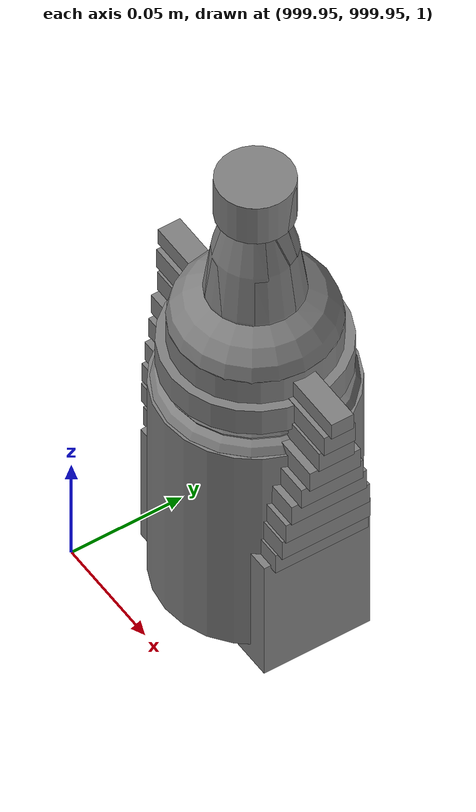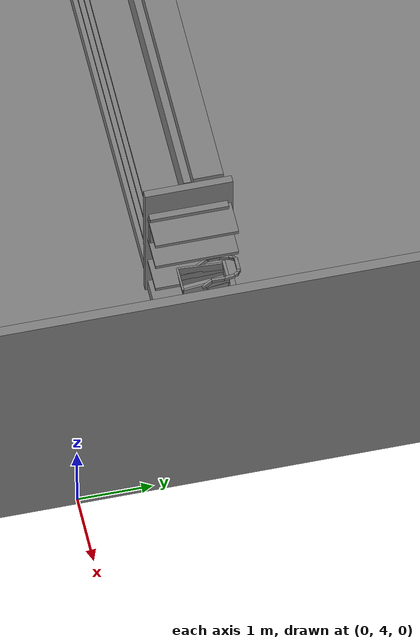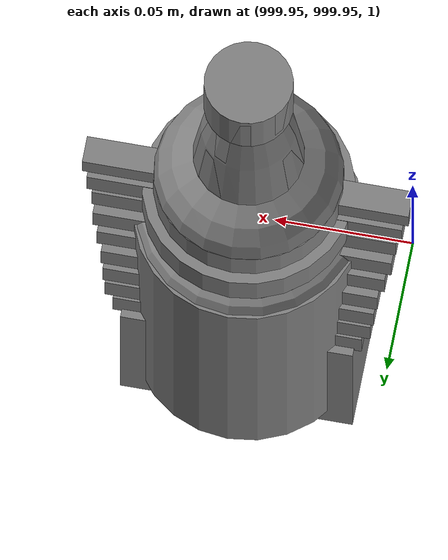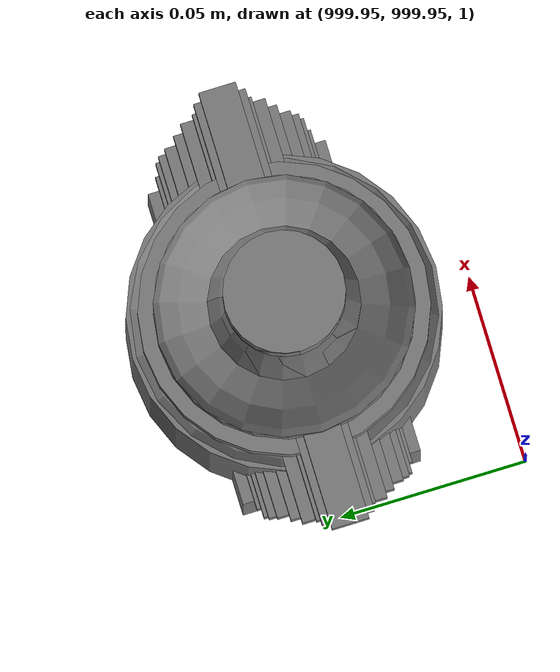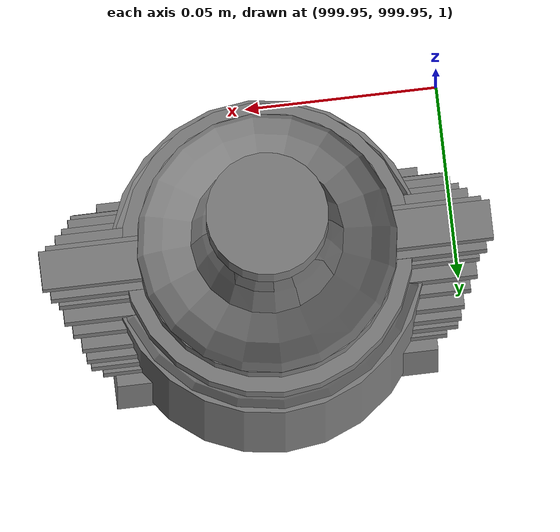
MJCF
<mujoco>
    <option gravity="0.000000000 0.000000000 -9.810000420" timestep="0.0166666" integrator="implicitfast" density="1.225" viscosity="1.8000001e-05" noslip_iterations="10" iterations="100" sdf_iterations="50">
        <flag multiccd="disable"/>
    </option>
    <size memory="1000M"/>
    <compiler coordinate="local"/>
    <worldbody>
        <light cutoff="30" pos="0 1 1" dir="0 -1 -2"/>
        <light cutoff="30" pos="0 -1 1" dir="0 1 -2"/>
        <body pos="0.000000000 0.000000000 0.000000000" euler="0.000000000 0.000000000 0.000000000" name="Interactive Objects_Interactive Objects"/>
        <body pos="1000.000000000 1000.000000000 1.000000000" euler="0.000000000 0.000000000 0.000000000" name="openloong_gripper_2f85_fix_base_usda_bottle_red">
            <geom contype="1" conaffinity="1" density="1000" type="ellipsoid" material="" rgba="0.500000000 0.500000000 0.500000000 1.000000000" solimp="0.899999976 0.949999988 0.001000000" friction="1.000000000 0.005000000 0.000100000" solref="0.020000000 1.000000000" margin="0" condim="3" group="0" pos="0.000000000 0.000000000 0.144284487" quat="1.000000000 0.000000000 0.000000000 0.000000000" size="0.021000000 0.021000000 0.079999998" name="openloong_gripper_2f85_fix_base_usda_geom_75E9F21E_51CA_4304_8723_10C5D2400E3B"/>
            <geom contype="1" conaffinity="1" density="1000" type="cylinder" material="" rgba="0.500000000 0.500000000 0.500000000 1.000000000" solimp="0.899999976 0.949999988 0.001000000" friction="1.000000000 0.005000000 0.000100000" solref="0.020000000 1.000000000" margin="0" condim="3" group="0" pos="0.000000000 0.000000000 0.220618963" quat="1.000000000 0.000000000 0.000000000 0.000000000" size="0.016000001 0.010000000 1.000000000" name="openloong_gripper_2f85_fix_base_usda_geom_26032BAC_8C50_43A0_90AA_191FDA690A86"/>
            <geom contype="1" conaffinity="1" density="1000" type="ellipsoid" material="" rgba="0.500000000 0.500000000 0.500000000 1.000000000" solimp="0.899999976 0.949999988 0.001000000" friction="1.000000000 0.005000000 0.000100000" solref="0.020000000 1.000000000" margin="0" condim="3" group="0" pos="0.000000000 0.000000000 0.118945479" quat="1.000000000 0.000000000 0.000000000 0.000000000" size="0.030999999 0.030999999 0.029999999" name="openloong_gripper_2f85_fix_base_usda_geom_5A0685B3_CAAF_4727_A286_5CFE6FDFADFB"/>
            <geom contype="1" conaffinity="1" density="1000" type="box" material="" rgba="0.500000000 0.500000000 0.500000000 1.000000000" solimp="0.899999976 0.949999988 0.001000000" friction="1.000000000 0.005000000 0.000100000" solref="0.020000000 1.000000000" margin="0" condim="3" group="0" pos="0.000000000 0.000000000 0.002189159" quat="1.000000000 0.000000000 0.000000000 0.000000000" size="0.020000000 0.020000000 0.003000000" name="openloong_gripper_2f85_fix_base_usda_geom_537DD00C_0902_4B79_878C_5C8802377726"/>
            <geom contype="1" conaffinity="1" density="1000" type="cylinder" material="" rgba="0.500000000 0.500000000 0.500000000 1.000000000" solimp="0.899999976 0.949999988 0.001000000" friction="1.000000000 0.005000000 0.000100000" solref="0.020000000 1.000000000" margin="0" condim="3" group="0" pos="0.000000000 -0.000366211 0.060884237" quat="1.000000000 0.000000000 0.000000000 0.000000000" size="0.030999999 0.057999998 1.000000000" name="openloong_gripper_2f85_fix_base_usda_geom_8C281B61_C065_45E7_B0A0_5DCCBFDE5FF1"/>
            <freejoint name="openloong_gripper_2f85_fix_base_usda_bottle_red_joint"/>
            <site size="0.005000000 0.005000000 0.005000000" rgba="0.500000000 0.500000000 0.500000000 1.000000000" pos="0.000000000 0.000000000 0.000000000" quat="0.999961913 0.008726535 0.000000000 0.000000000" group="0" type="sphere" name="openloong_gripper_2f85_fix_base_usda_bottle_redsite"/>
        </body>
        <body pos="1000.000000000 1000.000000000 1.000000000" euler="0.000000000 0.000000000 0.000000000" name="openloong_gripper_2f85_fix_base_usda_can">
            <geom contype="1" conaffinity="1" density="1000" type="cylinder" material="" rgba="0.500000000 0.500000000 0.500000000 1.000000000" solimp="0.899999976 0.949999988 0.001000000" friction="1.000000000 0.005000000 0.000100000" solref="0.020000000 1.000000000" margin="0" condim="3" group="0" pos="0.000000000 0.000000000 0.079676986" quat="1.000000000 0.000000000 0.000000000 0.000000000" size="0.034000002 0.071999997 1.000000000" name="openloong_gripper_2f85_fix_base_usda_geom_50F303B9_8FB3_4A3D_A626_AB96A59DFFCE"/>
            <geom contype="1" conaffinity="1" density="1000" type="ellipsoid" material="" rgba="0.500000000 0.500000000 0.500000000 1.000000000" solimp="0.899999976 0.949999988 0.001000000" friction="1.000000000 0.005000000 0.000100000" solref="0.020000000 1.000000000" margin="0" condim="3" group="0" pos="0.000000000 0.000000000 0.151854277" quat="1.000000000 0.000000000 0.000000000 0.000000000" size="0.034000002 0.034000002 0.020000000" name="openloong_gripper_2f85_fix_base_usda_geom_211E8A02_ED09_42B5_BE2F_49A90E9900A3"/>
            <geom contype="1" conaffinity="1" density="1000" type="box" material="" rgba="0.500000000 0.500000000 0.500000000 1.000000000" solimp="0.899999976 0.949999988 0.001000000" friction="1.000000000 0.005000000 0.000100000" solref="0.020000000 1.000000000" margin="0" condim="3" group="0" pos="0.000000000 0.000000000 0.004777670" quat="1.000000000 0.000000000 0.000000000 0.000000000" size="0.020000000 0.020000000 0.005000000" name="openloong_gripper_2f85_fix_base_usda_geom_4DEC2919_D173_4DF5_B7F7_6E8FBD265FB3"/>
            <freejoint name="openloong_gripper_2f85_fix_base_usda_can_joint"/>
            <site size="0.005000000 0.005000000 0.005000000" rgba="0.500000000 0.500000000 0.500000000 1.000000000" pos="0.000000000 0.000000000 0.000000000" quat="1.000000000 0.000000000 0.000000000 0.000000000" group="0" type="sphere" name="openloong_gripper_2f85_fix_base_usda_cansite"/>
        </body>
        <body pos="1000.000000000 1000.000000000 1.000000000" euler="0.000000000 0.000000000 0.000000000" name="openloong_gripper_2f85_fix_base_usda_jar_01">
            <geom contype="1" conaffinity="1" density="1000" type="box" material="" rgba="0.500000000 0.500000000 0.500000000 1.000000000" solimp="0.899999976 0.949999988 0.001000000" friction="1.000000000 0.005000000 0.000100000" solref="0.020000000 1.000000000" margin="0" condim="3" group="0" pos="0.000000000 0.000000000 0.006158113" quat="1.000000000 0.000000000 0.000000000 0.000000000" size="0.020000000 0.020000000 0.005000000" name="openloong_gripper_2f85_fix_base_usda_geom_176E3039_86EA_4ECF_9541_4E1964882421"/>
            <geom contype="1" conaffinity="1" density="1000" type="cylinder" material="" rgba="0.500000000 0.500000000 0.500000000 1.000000000" solimp="0.899999976 0.949999988 0.001000000" friction="1.000000000 0.005000000 0.000100000" solref="0.020000000 1.000000000" margin="0" condim="3" group="0" pos="0.000000000 0.000000000 0.062744498" quat="1.000000000 0.000000000 0.000000000 0.000000000" size="0.041000001 0.052999999 1.000000000" name="openloong_gripper_2f85_fix_base_usda_geom_6A1634CA_82CA_4D5A_A292_D9C4703D9960"/>
            <geom contype="1" conaffinity="1" density="1000" type="ellipsoid" material="" rgba="0.500000000 0.500000000 0.500000000 1.000000000" solimp="0.899999976 0.949999988 0.001000000" friction="1.000000000 0.005000000 0.000100000" solref="0.020000000 1.000000000" margin="0" condim="3" group="0" pos="0.000000000 0.000000000 0.122252703" quat="1.000000000 0.000000000 0.000000000 0.000000000" size="0.035999998 0.035999998 0.010000000" name="openloong_gripper_2f85_fix_base_usda_geom_A2BD285B_1C3E_4674_B388_A45626DB862C"/>
            <geom contype="1" conaffinity="1" density="1000" type="cylinder" material="" rgba="0.500000000 0.500000000 0.500000000 1.000000000" solimp="0.899999976 0.949999988 0.001000000" friction="1.000000000 0.005000000 0.000100000" solref="0.020000000 1.000000000" margin="0" condim="3" group="0" pos="0.000000000 0.000000000 0.015747190" quat="1.000000000 0.000000000 0.000000000 0.000000000" size="0.035000000 0.010000000 1.000000000" name="openloong_gripper_2f85_fix_base_usda_geom_341005DF_764B_4B1F_8000_C5A3A29DFF93"/>
            <geom contype="1" conaffinity="1" density="1000" type="ellipsoid" material="" rgba="0.500000000 0.500000000 0.500000000 1.000000000" solimp="0.899999976 0.949999988 0.001000000" friction="1.000000000 0.005000000 0.000100000" solref="0.020000000 1.000000000" margin="0" condim="3" group="0" pos="0.000000000 0.000000000 0.115815401" quat="1.000000000 0.000000000 0.000000000 0.000000000" size="0.039999999 0.039999999 0.010000000" name="openloong_gripper_2f85_fix_base_usda_geom_DD12E957_4A3B_479E_97F2_422085734824"/>
            <geom contype="1" conaffinity="1" density="1000" type="cylinder" material="" rgba="0.500000000 0.500000000 0.500000000 1.000000000" solimp="0.899999976 0.949999988 0.001000000" friction="1.000000000 0.005000000 0.000100000" solref="0.020000000 1.000000000" margin="0" condim="3" group="0" pos="0.000000000 0.000000000 0.133183479" quat="1.000000000 0.000000000 0.000000000 0.000000000" size="0.037999999 0.006500000 1.000000000" name="openloong_gripper_2f85_fix_base_usda_geom_E49BF1D9_D777_46E5_B9F2_860A9BF70D58"/>
            <freejoint name="openloong_gripper_2f85_fix_base_usda_jar_01_joint"/>
            <site size="0.005000000 0.005000000 0.005000000" rgba="0.500000000 0.500000000 0.500000000 1.000000000" pos="0.000000000 0.000000000 0.000000000" quat="1.000000000 0.000000000 0.000000000 0.000000000" group="0" type="sphere" name="openloong_gripper_2f85_fix_base_usda_jar_01site"/>
        </body>
        <body pos="-2.045918226 5.788069248 1.727471471" euler="-136.085174561 13.423933029 -106.780273438" mocap="true" name="spotlight5_SpotLight"/>
        <body pos="-2.154341936 5.753205776 1.764845133" euler="144.441024780 -64.617622375 162.953796387" mocap="true" name="spotlight1_SpotLight"/>
        <body pos="1000.000000000 1000.000000000 1.000000000" euler="0.000000000 0.000000000 0.000000000" name="openloong_gripper_2f85_fix_base_usda_bottle_blue">
            <geom contype="1" conaffinity="1" density="1000" type="ellipsoid" material="" rgba="0.500000000 0.500000000 0.500000000 1.000000000" solimp="0.899999976 0.949999988 0.001000000" friction="1.000000000 0.005000000 0.000100000" solref="0.020000000 1.000000000" margin="0" condim="3" group="0" pos="0.000000000 0.000000000 0.118920922" quat="1.000000000 0.000000000 0.000000000 0.000000000" size="0.030999999 0.030999999 0.029999999" name="openloong_gripper_2f85_fix_base_usda_geom_CBEACC23_4249_4F61_B03E_1EA920FC79DD"/>
            <geom contype="1" conaffinity="1" density="1000" type="box" material="" rgba="0.500000000 0.500000000 0.500000000 1.000000000" solimp="0.899999976 0.949999988 0.001000000" friction="1.000000000 0.005000000 0.000100000" solref="0.020000000 1.000000000" margin="0" condim="3" group="0" pos="0.000000000 0.000000000 0.002164602" quat="1.000000000 0.000000000 0.000000000 0.000000000" size="0.020000000 0.020000000 0.003000000" name="openloong_gripper_2f85_fix_base_usda_geom_137E60D4_EC67_479D_9757_3EAA76F80622"/>
            <geom contype="1" conaffinity="1" density="1000" type="cylinder" material="" rgba="0.500000000 0.500000000 0.500000000 1.000000000" solimp="0.899999976 0.949999988 0.001000000" friction="1.000000000 0.005000000 0.000100000" solref="0.020000000 1.000000000" margin="0" condim="3" group="0" pos="0.000000000 -0.000366211 0.060859680" quat="1.000000000 0.000000000 0.000000000 0.000000000" size="0.030999999 0.057999998 1.000000000" name="openloong_gripper_2f85_fix_base_usda_geom_43D70B01_D82C_4B95_9F7C_82BDD58D72ED"/>
            <geom contype="1" conaffinity="1" density="1000" type="cylinder" material="" rgba="0.500000000 0.500000000 0.500000000 1.000000000" solimp="0.899999976 0.949999988 0.001000000" friction="1.000000000 0.005000000 0.000100000" solref="0.020000000 1.000000000" margin="0" condim="3" group="0" pos="0.000000000 0.000000000 0.220594406" quat="1.000000000 0.000000000 0.000000000 0.000000000" size="0.016000001 0.010000000 1.000000000" name="openloong_gripper_2f85_fix_base_usda_geom_733D705F_6B50_4FEE_A788_F2B13895F9CD"/>
            <geom contype="1" conaffinity="1" density="1000" type="ellipsoid" material="" rgba="0.500000000 0.500000000 0.500000000 1.000000000" solimp="0.899999976 0.949999988 0.001000000" friction="1.000000000 0.005000000 0.000100000" solref="0.020000000 1.000000000" margin="0" condim="3" group="0" pos="0.000000000 0.000000000 0.144259930" quat="1.000000000 0.000000000 0.000000000 0.000000000" size="0.021000000 0.021000000 0.079999998" name="openloong_gripper_2f85_fix_base_usda_geom_2ADB1F30_3D6F_4AB3_A3E4_6479F4885D70"/>
            <freejoint name="openloong_gripper_2f85_fix_base_usda_bottle_blue_joint"/>
            <site size="0.005000000 0.005000000 0.005000000" rgba="0.500000000 0.500000000 0.500000000 1.000000000" pos="0.000000000 0.000000000 0.000000000" quat="0.999961913 0.008726535 0.000000000 0.000000000" group="0" type="sphere" name="openloong_gripper_2f85_fix_base_usda_bottle_bluesite"/>
        </body>
        <body pos="-2.350998163 6.299627781 1.807759643" euler="-126.101005554 44.519046783 -20.247262955" mocap="true" name="spotlight2_SpotLight"/>
        <body pos="1000.000000000 1000.000000000 1.000000000" euler="0.000000000 0.000000000 0.000000000" name="openloong_gripper_2f85_fix_base_usda_salt">
            <geom contype="1" conaffinity="1" density="1000" type="box" material="" rgba="0.500000000 0.500000000 0.500000000 1.000000000" solimp="0.899999976 0.949999988 0.001000000" friction="1.000000000 0.005000000 0.000100000" solref="0.020000000 1.000000000" margin="0" condim="3" group="0" pos="0.000305176 0.000000000 0.084862232" quat="1.000000000 0.000000000 0.000000000 0.000000000" size="0.048999999 0.018999999 0.005000000" name="openloong_gripper_2f85_fix_base_usda_geom_EEA11A4D_1FD7_4392_A0BD_D96498AB692F"/>
            <geom contype="1" conaffinity="1" density="1000" type="box" material="" rgba="0.500000000 0.500000000 0.500000000 1.000000000" solimp="0.899999976 0.949999988 0.001000000" friction="1.000000000 0.005000000 0.000100000" solref="0.020000000 1.000000000" margin="0" condim="3" group="0" pos="0.000305176 0.000000000 0.104564309" quat="1.000000000 0.000000000 0.000000000 0.000000000" size="0.052000001 0.014000000 0.005000000" name="openloong_gripper_2f85_fix_base_usda_geom_871CFDC4_C388_4F3F_9ADB_48F9E124E82E"/>
            <geom contype="1" conaffinity="1" density="1000" type="box" material="" rgba="0.500000000 0.500000000 0.500000000 1.000000000" solimp="0.899999976 0.949999988 0.001000000" friction="1.000000000 0.005000000 0.000100000" solref="0.020000000 1.000000000" margin="0" condim="3" group="0" pos="0.000305176 0.000000000 0.114487171" quat="1.000000000 0.000000000 0.000000000 0.000000000" size="0.054000001 0.011500000 0.005000000" name="openloong_gripper_2f85_fix_base_usda_geom_C97AA059_FE4F_4850_8BA6_F70C596D8D42"/>
            <geom contype="1" conaffinity="1" density="1000" type="box" material="" rgba="0.500000000 0.500000000 0.500000000 1.000000000" solimp="0.899999976 0.949999988 0.001000000" friction="1.000000000 0.005000000 0.000100000" solref="0.020000000 1.000000000" margin="0" condim="3" group="0" pos="0.000305176 0.000000000 0.075103164" quat="1.000000000 0.000000000 0.000000000 0.000000000" size="0.048000000 0.020000000 0.005000000" name="openloong_gripper_2f85_fix_base_usda_geom_B2408B34_0213_427A_A2E1_B53FB70DF959"/>
            <geom contype="1" conaffinity="1" density="1000" type="box" material="" rgba="0.500000000 0.500000000 0.500000000 1.000000000" solimp="0.899999976 0.949999988 0.001000000" friction="1.000000000 0.005000000 0.000100000" solref="0.020000000 1.000000000" margin="0" condim="3" group="0" pos="0.000305176 0.000000000 0.134892464" quat="1.000000000 0.000000000 0.000000000 0.000000000" size="0.057000000 0.007000000 0.005000000" name="openloong_gripper_2f85_fix_base_usda_geom_5590C55D_41DC_4427_8465_45C28FE72D01"/>
            <geom contype="1" conaffinity="1" density="1000" type="box" material="" rgba="0.500000000 0.500000000 0.500000000 1.000000000" solimp="0.899999976 0.949999988 0.001000000" friction="1.000000000 0.005000000 0.000100000" solref="0.020000000 1.000000000" margin="0" condim="3" group="0" pos="0.000305176 0.000000000 0.094920278" quat="1.000000000 0.000000000 0.000000000 0.000000000" size="0.050000001 0.017000001 0.005000000" name="openloong_gripper_2f85_fix_base_usda_geom_69EA031F_9C2E_44E3_AAC9_E95A28FD32A6"/>
            <geom contype="1" conaffinity="1" density="1000" type="box" material="" rgba="0.500000000 0.500000000 0.500000000 1.000000000" solimp="0.899999976 0.949999988 0.001000000" friction="1.000000000 0.005000000 0.000100000" solref="0.020000000 1.000000000" margin="0" condim="3" group="0" pos="0.000305176 0.000000000 0.065204859" quat="1.000000000 0.000000000 0.000000000 0.000000000" size="0.045000002 0.021000000 0.005000000" name="openloong_gripper_2f85_fix_base_usda_geom_26379E4C_A23B_4716_AC82_301D91BED0A6"/>
            <geom contype="1" conaffinity="1" density="1000" type="box" material="" rgba="0.500000000 0.500000000 0.500000000 1.000000000" solimp="0.899999976 0.949999988 0.001000000" friction="1.000000000 0.005000000 0.000100000" solref="0.020000000 1.000000000" margin="0" condim="3" group="0" pos="0.000305176 0.000000000 0.144135714" quat="1.000000000 0.000000000 0.000000000 0.000000000" size="0.059000000 0.005000000 0.004000000" name="openloong_gripper_2f85_fix_base_usda_geom_38E7EA98_0929_4154_AA05_64DFDC6786F8"/>
            <geom contype="1" conaffinity="1" density="1000" type="box" material="" rgba="0.500000000 0.500000000 0.500000000 1.000000000" solimp="0.899999976 0.949999988 0.001000000" friction="1.000000000 0.005000000 0.000100000" solref="0.020000000 1.000000000" margin="0" condim="3" group="0" pos="0.000000000 0.000000000 0.031593561" quat="1.000000000 0.000000000 0.000000000 0.000000000" size="0.041999999 0.024000000 0.029999999" name="openloong_gripper_2f85_fix_base_usda_geom_3772439C_BC90_4DE2_8788_3AE498594264"/>
            <geom contype="1" conaffinity="1" density="1000" type="box" material="" rgba="0.500000000 0.500000000 0.500000000 1.000000000" solimp="0.899999976 0.949999988 0.001000000" friction="1.000000000 0.005000000 0.000100000" solref="0.020000000 1.000000000" margin="0" condim="3" group="0" pos="0.000305176 0.000000000 0.124608755" quat="1.000000000 0.000000000 0.000000000 0.000000000" size="0.055000000 0.008000000 0.005000000" name="openloong_gripper_2f85_fix_base_usda_geom_E7D8AA26_A04F_48CC_9CE4_631DCF3688C9"/>
            <freejoint name="openloong_gripper_2f85_fix_base_usda_salt_joint"/>
            <site size="0.005000000 0.005000000 0.005000000" rgba="0.500000000 0.500000000 0.500000000 1.000000000" pos="0.000000000 0.000000000 0.000000000" quat="1.000000000 0.000000000 0.000000000 0.000000000" group="0" type="sphere" name="openloong_gripper_2f85_fix_base_usda_saltsite"/>
        </body>
        <body pos="0.000000000 0.000000000 0.000000000" euler="0.000000000 0.000000000 0.000000000" name=" Static Objects_ Static Objects">
            <geom contype="1" conaffinity="1" density="1000" type="box" material="" rgba="0.500000000 0.500000000 0.500000000 1.000000000" solimp="0.899999976 0.949999988 0.001000000" friction="1.000000000 0.005000000 0.000100000" solref="0.020000000 1.000000000" margin="0" condim="3" group="0" pos="-6.286010742 6.153595448 1.563861728" quat="0.707107067 0.000000000 0.000000000 0.707106471" size="0.529999971 3.134999990 0.025000000" name=" Static Objects_geom_847EBE13_2CBD_40EC_9F84_CC48D7ED9349"/>
            <geom contype="1" conaffinity="1" density="1000" type="box" material="" rgba="0.500000000 0.500000000 0.500000000 1.000000000" solimp="0.899999976 0.949999988 0.001000000" friction="1.000000000 0.005000000 0.000100000" solref="0.020000000 1.000000000" margin="0" condim="3" group="0" pos="-3.101639986 6.150595188 1.018643856" quat="1.000000000 0.000000000 0.000000000 0.000000000" size="0.050000001 0.579999983 1.019999981" name=" Static Objects_geom_63115B8A_BDA4_4AF5_853A_0F4AA617FA03"/>
            <geom contype="1" conaffinity="1" density="1000" type="box" material="" rgba="0.500000000 0.500000000 0.500000000 1.000000000" solimp="0.899999976 0.949999988 0.001000000" friction="1.000000000 0.005000000 0.000100000" solref="0.020000000 1.000000000" margin="0" condim="3" group="0" pos="-2.825197220 6.153595448 1.563861728" quat="0.707107067 0.000000000 0.000000000 0.707106471" size="0.550000012 0.239999995 0.025000000" name=" Static Objects_geom_64CC5376_FB54_4E83_B2AC_FFD078A103F9"/>
            <geom contype="1" conaffinity="1" density="1000" type="box" material="" rgba="0.500000000 0.500000000 0.500000000 1.000000000" solimp="0.899999976 0.949999988 0.001000000" friction="1.000000000 0.005000000 0.000100000" solref="0.020000000 1.000000000" margin="0" condim="3" group="0" pos="-6.311686516 6.153595448 1.018643856" quat="0.707107067 0.000000000 0.000000000 0.707106471" size="0.050000001 3.150000095 1.019999981" name=" Static Objects_geom_394E4E29_08C5_41FC_9C06_6E9B11E45A98"/>
            <geom contype="1" conaffinity="1" density="1000" type="box" material="" rgba="0.500000000 0.500000000 0.500000000 1.000000000" solimp="0.899999976 0.949999988 0.001000000" friction="1.000000000 0.005000000 0.000100000" solref="0.020000000 1.000000000" margin="0" condim="3" group="0" pos="-2.825197220 6.153595448 1.115278244" quat="0.707107067 0.000000000 0.000000000 0.707106471" size="0.550000012 0.239999995 0.025000000" name=" Static Objects_geom_DFE4D1EA_356C_431F_A034_393A3217127B"/>
            <geom contype="1" conaffinity="1" density="1000" type="box" material="" rgba="0.500000000 0.500000000 0.500000000 1.000000000" solimp="0.899999976 0.949999988 0.001000000" friction="1.000000000 0.005000000 0.000100000" solref="0.020000000 1.000000000" margin="0" condim="3" group="0" pos="-6.293097973 6.153595448 1.114443064" quat="0.707107067 0.000000000 0.000000000 0.707106471" size="0.529999971 3.134999990 0.025000000" name=" Static Objects_geom_DF8F6BE9_3292_4122_B617_DED07F57B4F4"/>
            <geom contype="1" conaffinity="1" density="1000" type="box" material="" rgba="0.500000000 0.500000000 0.500000000 1.000000000" solimp="0.899999976 0.949999988 0.001000000" friction="1.000000000 0.005000000 0.000100000" solref="0.020000000 1.000000000" margin="0" condim="3" group="0" pos="-2.825197220 6.153595448 0.629031777" quat="0.707107067 0.000000000 0.000000000 0.707106471" size="0.550000012 0.239999995 0.025000000" name=" Static Objects_geom_7BC53972_2247_4191_B707_3B8684763787"/>
            <geom contype="1" conaffinity="1" density="1000" type="box" material="" rgba="0.500000000 0.500000000 0.500000000 1.000000000" solimp="0.899999976 0.949999988 0.001000000" friction="1.000000000 0.005000000 0.000100000" solref="0.020000000 1.000000000" margin="0" condim="3" group="0" pos="-6.286010742 6.153595448 0.096129179" quat="0.707107067 0.000000000 0.000000000 0.707106471" size="0.529999971 3.134999990 0.098999999" name=" Static Objects_geom_8AFCF142_5F61_446B_8175_1BCBCD416787"/>
            <geom contype="1" conaffinity="1" density="1000" type="box" material="" rgba="0.500000000 0.500000000 0.500000000 1.000000000" solimp="0.899999976 0.949999988 0.001000000" friction="1.000000000 0.005000000 0.000100000" solref="0.020000000 1.000000000" margin="0" condim="3" group="0" pos="-2.825197220 6.153595448 0.097434282" quat="0.707107067 0.000000000 0.000000000 0.707106471" size="0.550000012 0.239999995 0.098999999" name=" Static Objects_geom_982B79D0_8117_414D_AEF1_E587E157F6F8"/>
            <geom contype="1" conaffinity="1" density="1000" type="box" material="" rgba="0.500000000 0.500000000 0.500000000 1.000000000" solimp="0.899999976 0.949999988 0.001000000" friction="1.000000000 0.005000000 0.000100000" solref="0.020000000 1.000000000" margin="0" condim="3" group="0" pos="-6.286010742 6.153595448 0.629031777" quat="0.707107067 0.000000000 0.000000000 0.707106471" size="0.529999971 3.134999990 0.025000000" name=" Static Objects_geom_C6034358_D171_4295_8F58_D3375F5909DD"/>
            <geom contype="1" conaffinity="1" density="1000" type="box" material="" rgba="0.500000000 0.500000000 0.500000000 1.000000000" solimp="0.899999976 0.949999988 0.001000000" friction="1.000000000 0.005000000 0.000100000" solref="0.020000000 1.000000000" margin="0" condim="3" group="0" pos="-6.000000000 20.159999847 2.000000000" quat="1.000000000 0.000000000 0.000000000 0.000000000" size="6.079999924 0.070000000 2.000000000" name=" Static Objects_geom_5D92893C_B144_4524_B620_B819627BE28A"/>
            <geom contype="1" conaffinity="1" density="1000" type="box" material="" rgba="0.500000000 0.500000000 0.500000000 1.000000000" solimp="0.899999976 0.949999988 0.001000000" friction="1.000000000 0.005000000 0.000100000" solref="0.020000000 1.000000000" margin="0" condim="3" group="0" pos="-6.000000000 0.035000000 2.000000000" quat="1.000000000 0.000000000 0.000000000 0.000000000" size="6.079999924 0.070000000 2.000000000" name=" Static Objects_geom_20259EB1_8072_4773_ABA5_D96EF7590AA6"/>
            <geom contype="1" conaffinity="1" density="1000" type="box" material="" rgba="0.500000000 0.500000000 0.500000000 1.000000000" solimp="0.899999976 0.949999988 0.001000000" friction="1.000000000 0.005000000 0.000100000" solref="0.020000000 1.000000000" margin="0" condim="3" group="0" pos="0.000000000 10.000000000 2.000000000" quat="1.000000000 0.000000000 0.000000000 0.000000000" size="0.070000000 10.500000000 2.000000000" name=" Static Objects_geom_973BD024_61E3_4BBF_8D90_D860B49C6648"/>
            <geom contype="1" conaffinity="1" density="1000" type="box" material="" rgba="0.500000000 0.500000000 0.500000000 1.000000000" solimp="0.899999976 0.949999988 0.001000000" friction="1.000000000 0.005000000 0.000100000" solref="0.020000000 1.000000000" margin="0" condim="3" group="0" pos="-12.050000191 10.000000000 2.000000000" quat="1.000000000 0.000000000 0.000000000 0.000000000" size="0.070000000 10.500000000 2.000000000" name=" Static Objects_geom_42C3E8D7_ADB6_4072_896E_E6BFE407762A"/>
            <geom contype="1" conaffinity="1" density="1000" type="plane" material="" rgba="0.500000000 0.500000000 0.500000000 1.000000000" solimp="0.899999976 0.949999988 0.001000000" friction="1.000000000 0.005000000 0.000100000" solref="0.020000000 1.000000000" margin="0" condim="3" group="0" pos="-6.000000000 10.399999619 0.000000000" quat="1.000000000 0.000000000 0.000000000 0.000000000" size="6.050000191 10.800000191 0.010000000" name=" Static Objects_geom_B640FDB9_09E4_4084_B776_5CFB4A88AA6E"/>
            <geom contype="1" conaffinity="1" density="1000" type="box" material="" rgba="0.500000000 0.500000000 0.500000000 1.000000000" solimp="0.899999976 0.949999988 0.001000000" friction="1.000000000 0.005000000 0.000100000" solref="0.020000000 1.000000000" margin="0" condim="3" group="0" pos="-8.830721855 2.096410990 0.549305558" quat="1.000000000 0.000000000 0.000000000 0.000000000" size="0.280000001 0.430000007 0.550000012" name=" Static Objects_geom_05D0F032_B18C_4BE3_A560_8E60C3A35603"/>
            <geom contype="1" conaffinity="1" density="1000" type="box" material="" rgba="0.500000000 0.500000000 0.500000000 1.000000000" solimp="0.899999976 0.949999988 0.001000000" friction="1.000000000 0.005000000 0.000100000" solref="0.020000000 1.000000000" margin="0" condim="3" group="0" pos="-6.460197449 2.937205315 0.548931718" quat="1.000000000 0.000000000 0.000000000 0.000000000" size="2.650000095 0.430000007 0.550000012" name=" Static Objects_geom_BFFF70B1_75EE_4D6F_B36C_EC4B6A38A7C2"/>
            <geom contype="1" conaffinity="1" density="1000" type="box" material="" rgba="0.500000000 0.500000000 0.500000000 1.000000000" solimp="0.899999976 0.949999988 0.001000000" friction="1.000000000 0.005000000 0.000100000" solref="0.020000000 1.000000000" margin="0" condim="3" group="0" pos="-4.240264893 1.327049494 0.549888909" quat="1.000000000 0.000000000 0.000000000 0.000000000" size="0.430000007 1.200000048 0.550000012" name=" Static Objects_geom_E8E0D815_5EA3_4E0C_884D_5F8A8B4A7F46"/>
            <geom contype="1" conaffinity="1" density="1000" type="box" material="" rgba="0.500000000 0.500000000 0.500000000 1.000000000" solimp="0.899999976 0.949999988 0.001000000" friction="1.000000000 0.005000000 0.000100000" solref="0.020000000 1.000000000" margin="0" condim="3" group="0" pos="-7.408766270 3.088089943 1.776644945" quat="0.928051054 0.000000000 0.000000000 0.372453064" size="0.050000001 0.100000001 0.050000001" name=" Static Objects_geom_76163133_8CD6_4D06_A404_1918847DA9B2"/>
            <geom contype="1" conaffinity="1" density="1000" type="box" material="" rgba="0.500000000 0.500000000 0.500000000 1.000000000" solimp="0.899999976 0.949999988 0.001000000" friction="1.000000000 0.005000000 0.000100000" solref="0.020000000 1.000000000" margin="0" condim="3" group="0" pos="-7.437745571 3.067511320 1.289965630" quat="1.000000000 0.000000000 0.000000000 0.000000000" size="0.029999999 0.020000000 0.020000000" name=" Static Objects_geom_068CB7A6_4D5E_4483_A7C7_0E49C2BC7A3C"/>
            <geom contype="1" conaffinity="1" density="1000" type="box" material="" rgba="0.500000000 0.500000000 0.500000000 1.000000000" solimp="0.899999976 0.949999988 0.001000000" friction="1.000000000 0.005000000 0.000100000" solref="0.020000000 1.000000000" margin="0" condim="3" group="0" pos="-7.719123363 2.867671013 1.173410416" quat="1.000000000 0.000000000 0.000000000 0.000000000" size="0.250000000 0.250000000 0.079999998" name=" Static Objects_geom_867DFDD6_7D63_42C0_8429_ACB00ACACD1C"/>
            <geom contype="1" conaffinity="1" density="1000" type="box" material="" rgba="0.500000000 0.500000000 0.500000000 1.000000000" solimp="0.899999976 0.949999988 0.001000000" friction="1.000000000 0.005000000 0.000100000" solref="0.020000000 1.000000000" margin="0" condim="3" group="0" pos="-7.719123363 2.958004713 1.530241251" quat="1.000000000 0.000000000 0.000000000 0.000000000" size="0.250000000 0.159999996 0.280000001" name=" Static Objects_geom_482843A8_F3BA_40B3_A008_E3D95B39A746"/>
            <geom contype="1" conaffinity="1" density="1000" type="cylinder" material="" rgba="0.500000000 0.500000000 0.500000000 1.000000000" solimp="0.899999976 0.949999988 0.001000000" friction="1.000000000 0.005000000 0.000100000" solref="0.020000000 1.000000000" margin="0" condim="3" group="0" pos="-7.427312374 3.069516420 1.502544641" quat="0.928051054 0.000000000 0.000000000 0.372453064" size="0.015000000 0.230000004 0.100000001" name=" Static Objects_geom_AC53A48A_EB57_4FB0_BBCC_A051416598B3"/>
            <geom contype="1" conaffinity="1" density="1000" type="box" material="" rgba="0.500000000 0.500000000 0.500000000 1.000000000" solimp="0.899999976 0.949999988 0.001000000" friction="1.000000000 0.005000000 0.000100000" solref="0.020000000 1.000000000" margin="0" condim="3" group="0" pos="-9.058088303 6.434794426 1.209077358" quat="1.000000000 0.000000000 0.000000000 0.000000000" size="0.250000000 0.100000001 0.070000000" name=" Static Objects_geom_B1EB7086_3DE6_48B0_B07E_D47FAAC6391B"/>
            <geom contype="1" conaffinity="1" density="1000" type="box" material="" rgba="0.500000000 0.500000000 0.500000000 1.000000000" solimp="0.899999976 0.949999988 0.001000000" friction="1.000000000 0.005000000 0.000100000" solref="0.020000000 1.000000000" margin="0" condim="3" group="0" pos="-5.611940861 6.318420410 0.350975692" quat="1.000000000 0.000000000 0.000000000 0.000000000" size="0.699999988 0.100000001 0.150000006" name=" Static Objects_geom_F5677F4B_60FE_46FC_B1D2_EB639DACA5BF"/>
            <geom contype="1" conaffinity="1" density="1000" type="box" material="" rgba="0.500000000 0.500000000 0.500000000 1.000000000" solimp="0.899999976 0.949999988 0.001000000" friction="1.000000000 0.005000000 0.000100000" solref="0.020000000 1.000000000" margin="0" condim="3" group="0" pos="-9.237723351 6.464855671 1.209077358" quat="1.000000000 0.000000000 0.000000000 0.000000000" size="0.100000001 0.100000001 0.070000000" name=" Static Objects_geom_D51E1185_156A_44AE_A099_561130383E0D"/>
            <geom contype="1" conaffinity="1" density="1000" type="box" material="" rgba="0.500000000 0.500000000 0.500000000 1.000000000" solimp="0.899999976 0.949999988 0.001000000" friction="1.000000000 0.005000000 0.000100000" solref="0.020000000 1.000000000" margin="0" condim="3" group="0" pos="-6.300771236 6.459744930 1.744376063" quat="1.000000000 0.000000000 0.000000000 0.000000000" size="3.000000000 0.200000003 0.150000006" name=" Static Objects_geom_0BA500CF_32BD_46F6_819D_CDBC446A3E03"/>
            <geom contype="1" conaffinity="1" density="1000" type="box" material="" rgba="0.500000000 0.500000000 0.500000000 1.000000000" solimp="0.899999976 0.949999988 0.001000000" friction="1.000000000 0.005000000 0.000100000" solref="0.020000000 1.000000000" margin="0" condim="3" group="0" pos="-7.373087406 6.458900928 1.214329123" quat="1.000000000 0.000000000 0.000000000 0.000000000" size="0.250000000 0.200000003 0.075000003" name=" Static Objects_geom_2EFF5A7A_619E_4066_85EB_5A13921BEFAF"/>
            <geom contype="1" conaffinity="1" density="1000" type="box" material="" rgba="0.500000000 0.500000000 0.500000000 1.000000000" solimp="0.899999976 0.949999988 0.001000000" friction="1.000000000 0.005000000 0.000100000" solref="0.020000000 1.000000000" margin="0" condim="3" group="0" pos="-4.035642624 6.459744930 0.352518857" quat="1.000000000 0.000000000 0.000000000 0.000000000" size="0.800000012 0.200000003 0.150000006" name=" Static Objects_geom_885B4F22_9696_47B3_BA2B_E97E0B3DF1C7"/>
            <geom contype="1" conaffinity="1" density="1000" type="box" material="" rgba="0.500000000 0.500000000 0.500000000 1.000000000" solimp="0.899999976 0.949999988 0.001000000" friction="1.000000000 0.005000000 0.000100000" solref="0.020000000 1.000000000" margin="0" condim="3" group="0" pos="-3.907610416 6.318625927 0.800981164" quat="1.000000000 0.000000000 0.000000000 0.000000000" size="0.500000000 0.100000001 0.150000006" name=" Static Objects_geom_9672FC20_3A73_48D2_9CB7_ED725FEF7DCF"/>
            <geom contype="1" conaffinity="1" density="1000" type="box" material="" rgba="0.500000000 0.500000000 0.500000000 1.000000000" solimp="0.899999976 0.949999988 0.001000000" friction="1.000000000 0.005000000 0.000100000" solref="0.020000000 1.000000000" margin="0" condim="3" group="0" pos="-6.098561764 6.327973843 1.292199373" quat="1.000000000 0.000000000 0.000000000 0.000000000" size="0.500000000 0.100000001 0.150000006" name=" Static Objects_geom_4B568377_E8A1_4844_97E1_73BE8861F9FF"/>
            <geom contype="1" conaffinity="1" density="1000" type="box" material="" rgba="0.500000000 0.500000000 0.500000000 1.000000000" solimp="0.899999976 0.949999988 0.001000000" friction="1.000000000 0.005000000 0.000100000" solref="0.020000000 1.000000000" margin="0" condim="3" group="0" pos="-7.886891365 6.459744930 0.352518857" quat="1.000000000 0.000000000 0.000000000 0.000000000" size="1.500000000 0.200000003 0.150000006" name=" Static Objects_geom_49995B1A_44D1_4C2D_89EE_1D647E6C35E2"/>
            <geom contype="1" conaffinity="1" density="1000" type="box" material="" rgba="0.500000000 0.500000000 0.500000000 1.000000000" solimp="0.899999976 0.949999988 0.001000000" friction="1.000000000 0.005000000 0.000100000" solref="0.020000000 1.000000000" margin="0" condim="3" group="0" pos="-6.824534416 6.447464466 1.212718010" quat="1.000000000 0.000000000 0.000000000 0.000000000" size="0.100000001 0.100000001 0.075000003" name=" Static Objects_geom_7673CBD3_94D8_42CF_9373_A0F8C76649C9"/>
            <geom contype="1" conaffinity="1" density="1000" type="box" material="" rgba="0.500000000 0.500000000 0.500000000 1.000000000" solimp="0.899999976 0.949999988 0.001000000" friction="1.000000000 0.005000000 0.000100000" solref="0.020000000 1.000000000" margin="0" condim="3" group="0" pos="-4.407354832 6.459744930 1.292199373" quat="1.000000000 0.000000000 0.000000000 0.000000000" size="1.240000010 0.200000003 0.150000006" name=" Static Objects_geom_CCF80827_3B2B_4D41_BFE0_9B4F69803D9C"/>
            <geom contype="1" conaffinity="1" density="1000" type="box" material="" rgba="0.500000000 0.500000000 0.500000000 1.000000000" solimp="0.899999976 0.949999988 0.001000000" friction="1.000000000 0.005000000 0.000100000" solref="0.020000000 1.000000000" margin="0" condim="3" group="0" pos="-6.751636982 6.459744930 0.800981164" quat="1.000000000 0.000000000 0.000000000 0.000000000" size="2.200000048 0.200000003 0.150000006" name=" Static Objects_geom_83D03CA8_F851_42D4_B6E6_4136AED7D962"/>
            <geom contype="1" conaffinity="1" density="1000" type="box" material="" rgba="0.500000000 0.500000000 0.500000000 1.000000000" solimp="0.899999976 0.949999988 0.001000000" friction="1.000000000 0.005000000 0.000100000" solref="0.020000000 1.000000000" margin="0" condim="3" group="0" pos="-6.924745083 6.362090111 1.214329123" quat="1.000000000 0.000000000 0.000000000 0.000000000" size="0.200000003 0.100000001 0.075000003" name=" Static Objects_geom_D7D25FFC_B83E_45F8_A54F_7A23474DBBF9"/>
            <geom contype="1" conaffinity="1" density="1000" type="box" material="" rgba="0.500000000 0.500000000 0.500000000 1.000000000" solimp="0.899999976 0.949999988 0.001000000" friction="1.000000000 0.005000000 0.000100000" solref="0.020000000 1.000000000" margin="0" condim="3" group="0" pos="-8.844120979 6.464855671 1.209077358" quat="1.000000000 0.000000000 0.000000000 0.000000000" size="0.100000001 0.100000001 0.070000000" name=" Static Objects_geom_5BEEF1C6_D63F_4413_B326_9267F0CA10B3"/>
            <geom contype="1" conaffinity="1" density="1000" type="box" material="" rgba="0.500000000 0.500000000 0.500000000 1.000000000" solimp="0.899999976 0.949999988 0.001000000" friction="1.000000000 0.005000000 0.000100000" solref="0.020000000 1.000000000" margin="0" condim="3" group="0" pos="-3.157672644 6.136868477 1.348373055" quat="1.000000000 0.000000000 0.000000000 0.000000000" size="0.200000003 0.519999981 0.300000012" name=" Static Objects_geom_6C9E42A1_D361_48A2_842B_E58B34B9AFB7"/>
        </body>
        <body pos="-6.332345009 2.779978037 1.034067392" euler="0.000000000 0.000000000 0.000000000" name="openloong_gripper_2f85_fix_base_usda_basket">
            <geom contype="1" conaffinity="1" density="100000" type="box" material="" rgba="0.500000000 0.500000000 0.500000000 1.000000000" solimp="0.899999976 0.949999988 0.001000000" friction="1.000000000 0.899999976 0.000100000" solref="0.020000000 1.000000000" margin="0" condim="3" group="0" pos="-0.039724827 -0.188568115 0.167089701" quat="0.997537494 0.070135131 0.000000000 0.000000000" size="0.150000006 0.006000000 0.108000003" name="openloong_gripper_2f85_fix_base_usda_geom_D1139753_1114_44BB_9502_08E109991434"/>
            <geom contype="1" conaffinity="1" density="100000" type="box" material="" rgba="0.500000000 0.500000000 0.500000000 1.000000000" solimp="0.899999976 0.949999988 0.001000000" friction="1.000000000 0.899999976 0.000100000" solref="0.020000000 1.000000000" margin="0" condim="3" group="0" pos="0.094372749 0.000000000 0.168361664" quat="0.706172049 0.036353335 0.036353379 0.706171215" size="0.200000003 0.006000000 0.108000003" name="openloong_gripper_2f85_fix_base_usda_geom_AAFF72B5_F8A5_432A_A389_5F5F9499F301"/>
            <geom contype="1" conaffinity="1" density="100000" type="box" material="" rgba="0.500000000 0.500000000 0.500000000 1.000000000" solimp="0.899999976 0.949999988 0.001000000" friction="1.000000000 0.899999976 0.000100000" solref="0.020000000 1.000000000" margin="0" condim="3" group="0" pos="-0.039724827 0.000000000 0.068126202" quat="1.000000000 0.000000000 0.000000000 0.000000000" size="0.129999995 0.174999997 0.006000000" name="openloong_gripper_2f85_fix_base_usda_geom_B7665F6F_EF04_404B_8B5B_9D71F7DA45FC"/>
            <geom contype="1" conaffinity="1" density="100000" type="box" material="" rgba="0.500000000 0.500000000 0.500000000 1.000000000" solimp="0.899999976 0.949999988 0.001000000" friction="1.000000000 0.899999976 0.000100000" solref="0.020000000 1.000000000" margin="0" condim="3" group="0" pos="-0.039724827 0.188377380 0.167089701" quat="0.997489929 -0.070808925 0.000000000 0.000000000" size="0.150000006 0.006000000 0.108000003" name="openloong_gripper_2f85_fix_base_usda_geom_1789C714_7FC3_4A1D_B1BB_6010E3AC9D0F"/>
            <geom contype="1" conaffinity="1" density="100000" type="box" material="" rgba="0.500000000 0.500000000 0.500000000 1.000000000" solimp="0.899999976 0.949999988 0.001000000" friction="1.000000000 0.899999976 0.000100000" solref="0.020000000 1.000000000" margin="0" condim="3" group="0" pos="-0.172339439 0.000000000 0.168361664" quat="0.706172407 -0.036353018 -0.036353093 0.706170976" size="0.200000003 0.006000000 0.108000003" name="openloong_gripper_2f85_fix_base_usda_geom_9266D07C_7A0E_4404_B7FA_C5FED21AE236"/>
            <freejoint name="openloong_gripper_2f85_fix_base_usda_basket_joint"/>
            <site size="0.005000000 0.005000000 0.005000000" rgba="0.500000000 0.500000000 0.500000000 1.000000000" pos="0.000000000 0.000000000 0.000000000" quat="1.000000000 0.000000000 0.000000000 0.000000000" group="0" type="sphere" name="openloong_gripper_2f85_fix_base_usda_basketsite"/>
        </body>
        <body pos="-3.510578632 3.403555870 -0.000000100" euler="0.000000000 0.000000000 40.200675964" name="openloong_gripper_2f85_fix_base_usda_PZ">
            <geom contype="1" conaffinity="1" density="1000" type="box" material="" rgba="0.500000000 0.500000000 0.500000000 1.000000000" solimp="0.899999976 0.949999988 0.001000000" friction="1.000000000 0.005000000 0.000100000" solref="0.020000000 1.000000000" margin="0" condim="3" group="0" pos="-0.047453165 0.056484699 0.373715430" quat="0.934750080 0.077914521 0.028795123 0.345459938" size="0.180000007 0.010000000 0.379999995" name="openloong_gripper_2f85_fix_base_usda_geom_F2D6637B_C474_4869_BA0C_6EF9328C8277"/>
            <geom contype="1" conaffinity="1" density="1000" type="box" material="" rgba="0.500000000 0.500000000 0.500000000 1.000000000" solimp="0.899999976 0.949999988 0.001000000" friction="1.000000000 0.005000000 0.000100000" solref="0.020000000 1.000000000" margin="0" condim="3" group="0" pos="0.047452450 -0.054376602 0.374072611" quat="0.934387863 -0.082143910 -0.030358355 0.345326364" size="0.180000007 0.010000000 0.379999995" name="openloong_gripper_2f85_fix_base_usda_geom_95806291_66D6_4301_9412_F654BA66A5ED"/>
            <freejoint name="openloong_gripper_2f85_fix_base_usda_PZ"/>
        </body>
        <body pos="-7.168000221 2.823999882 1.227496982" euler="-0.283413976 0.056829724 -0.133293271" name="openloong_gripper_2f85_fix_base_usda_Pos">
            <geom contype="1" conaffinity="1" density="1000" type="box" material="" rgba="0.500000000 0.500000000 0.500000000 1.000000000" solimp="0.899999976 0.949999988 0.001000000" friction="1.000000000 0.005000000 0.000100000" solref="0.020000000 1.000000000" margin="0" condim="3" group="0" pos="-0.002278805 0.074524641 -0.004134059" quat="0.315989345 0.948763072 -0.000000000 0.000000000" size="0.059999999 0.013000000 0.035000000" name="openloong_gripper_2f85_fix_base_usda_geom_BC456051_2FFF_4858_BDBD_E1BC6217EAFE"/>
            <geom contype="1" conaffinity="1" density="1000" type="box" material="" rgba="0.500000000 0.500000000 0.500000000 1.000000000" solimp="0.899999976 0.949999988 0.001000000" friction="1.000000000 0.005000000 0.000100000" solref="0.020000000 1.000000000" margin="0" condim="3" group="0" pos="-0.002278805 0.078031301 0.008128285" quat="0.990447521 -0.137893379 -0.000000000 -0.000000000" size="0.059999999 0.010000000 0.035000000" name="openloong_gripper_2f85_fix_base_usda_geom_05F2D6F2_1E41_4CF4_BA67_FA166BFAEC1C"/>
            <geom contype="1" conaffinity="1" density="1000" type="box" material="" rgba="0.500000000 0.500000000 0.500000000 1.000000000" solimp="0.899999976 0.949999988 0.001000000" friction="1.000000000 0.005000000 0.000100000" solref="0.020000000 1.000000000" margin="0" condim="3" group="0" pos="-0.002278805 0.080785275 -0.002596974" quat="0.287325472 -0.957833409 0.000000000 -0.000000000" size="0.059999999 0.013000000 0.035000000" name="openloong_gripper_2f85_fix_base_usda_geom_7E244DD7_1A80_446B_A93D_647383EAE154"/>
            <geom contype="1" conaffinity="1" density="1000" type="box" material="" rgba="0.500000000 0.500000000 0.500000000 1.000000000" solimp="0.899999976 0.949999988 0.001000000" friction="1.000000000 0.005000000 0.000100000" solref="0.020000000 1.000000000" margin="0" condim="3" group="0" pos="-0.002278805 -0.098804474 -0.020146966" quat="0.988851666 0.148906454 0.000000000 -0.000000000" size="0.059999999 0.022000000 0.020000000" name="openloong_gripper_2f85_fix_base_usda_geom_5495AF24_AED7_452B_9556_E79895DEC53C"/>
            <geom contype="1" conaffinity="1" density="1000" type="box" material="" rgba="0.500000000 0.500000000 0.500000000 1.000000000" solimp="0.899999976 0.949999988 0.001000000" friction="1.000000000 0.005000000 0.000100000" solref="0.020000000 1.000000000" margin="0" condim="3" group="0" pos="-0.002279282 0.019920111 0.012102962" quat="0.995421767 0.095583342 -0.000000000 -0.000000000" size="0.059999999 0.025000000 0.026000001" name="openloong_gripper_2f85_fix_base_usda_geom_12251AF5_1A0A_4AA1_BF57_6F9F9A844B58"/>
            <geom contype="1" conaffinity="1" density="1000" type="box" material="" rgba="0.500000000 0.500000000 0.500000000 1.000000000" solimp="0.899999976 0.949999988 0.001000000" friction="1.000000000 0.005000000 0.000100000" solref="0.020000000 1.000000000" margin="0" condim="3" group="0" pos="-0.002279282 0.005734444 -0.014276862" quat="0.999571741 -0.029275302 -0.000000000 -0.000000000" size="0.059999999 0.050000001 0.010000000" name="openloong_gripper_2f85_fix_base_usda_geom_EB93C24E_62BD_4251_9ED0_63ACDAE1F8D5"/>
            <geom contype="1" conaffinity="1" density="1000" type="box" material="" rgba="0.500000000 0.500000000 0.500000000 1.000000000" solimp="0.899999976 0.949999988 0.001000000" friction="1.000000000 0.005000000 0.000100000" solref="0.020000000 1.000000000" margin="0" condim="3" group="0" pos="-0.002278805 0.079460382 0.007771969" quat="0.922590554 -0.385781586 0.000000000 -0.000000000" size="0.059999999 0.010000000 0.035000000" name="openloong_gripper_2f85_fix_base_usda_geom_DC1F0F82_B5D3_4882_B7E8_E1C075249211"/>
            <geom contype="1" conaffinity="1" density="1000" type="box" material="" rgba="0.500000000 0.500000000 0.500000000 1.000000000" solimp="0.899999976 0.949999988 0.001000000" friction="1.000000000 0.005000000 0.000100000" solref="0.020000000 1.000000000" margin="0" condim="3" group="0" pos="-0.002279282 0.081384182 -0.001320124" quat="0.590483785 -0.807049930 0.000000000 -0.000000000" size="0.059999999 0.013000000 0.035000000" name="openloong_gripper_2f85_fix_base_usda_geom_B745DB15_B655_4CF8_8D74_3B1CB940335C"/>
            <geom contype="1" conaffinity="1" density="1000" type="box" material="" rgba="0.500000000 0.500000000 0.500000000 1.000000000" solimp="0.899999976 0.949999988 0.001000000" friction="1.000000000 0.005000000 0.000100000" solref="0.020000000 1.000000000" margin="0" condim="3" group="0" pos="-0.002278805 -0.059297800 -0.007972836" quat="0.988851666 0.148906454 0.000000000 -0.000000000" size="0.059999999 0.020000000 0.022000000" name="openloong_gripper_2f85_fix_base_usda_geom_E5411F00_B1D6_480B_8E79_709A160CA84A"/>
            <geom contype="1" conaffinity="1" density="1000" type="box" material="" rgba="0.500000000 0.500000000 0.500000000 1.000000000" solimp="0.899999976 0.949999988 0.001000000" friction="1.000000000 0.005000000 0.000100000" solref="0.020000000 1.000000000" margin="0" condim="3" group="0" pos="-0.002278805 0.076618671 -0.004656792" quat="0.004634961 0.999989629 -0.000000000 0.000000000" size="0.059999999 0.013000000 0.035000000" name="openloong_gripper_2f85_fix_base_usda_geom_FDC1D76D_DCDE_4BD9_8722_54F23A51E823"/>
            <geom contype="1" conaffinity="1" density="1000" type="box" material="" rgba="0.500000000 0.500000000 0.500000000 1.000000000" solimp="0.899999976 0.949999988 0.001000000" friction="1.000000000 0.005000000 0.000100000" solref="0.020000000 1.000000000" margin="0" condim="3" group="0" pos="-0.002279282 -0.021952629 0.002960086" quat="0.991270423 0.131847665 -0.000000000 0.000000000" size="0.059999999 0.020000000 0.024000000" name="openloong_gripper_2f85_fix_base_usda_geom_1878D2ED_7DF0_4A00_AB56_056AE9BDEFFB"/>
            <geom contype="1" conaffinity="1" density="1000" type="box" material="" rgba="0.500000000 0.500000000 0.500000000 1.000000000" solimp="0.899999976 0.949999988 0.001000000" friction="1.000000000 0.005000000 0.000100000" solref="0.020000000 1.000000000" margin="0" condim="3" group="0" pos="-0.002278805 0.081418991 0.002587914" quat="0.803492308 -0.595315695 0.000000000 -0.000000000" size="0.059999999 0.013000000 0.035000000" name="openloong_gripper_2f85_fix_base_usda_geom_6527604F_AFA0_413E_888C_DA3C8BAA598F"/>
            <geom contype="1" conaffinity="1" density="1000" type="box" material="" rgba="0.500000000 0.500000000 0.500000000 1.000000000" solimp="0.899999976 0.949999988 0.001000000" friction="1.000000000 0.005000000 0.000100000" solref="0.020000000 1.000000000" margin="0" condim="3" group="0" pos="-0.002278805 0.061115503 0.008545756" quat="0.999326169 0.036714450 0.000000000 -0.000000000" size="0.059999999 0.020000000 0.035000000" name="openloong_gripper_2f85_fix_base_usda_geom_DFFCD53A_1BE1_4D49_B0E2_1715EF59DA38"/>
            <freejoint name="openloong_gripper_2f85_fix_base_usda_pos_scan"/>
        </body>
        <body pos="-2.436573029 6.404376507 0.137849092" euler="0.000000000 0.000000000 0.000000000" name="openloong_gripper_2f85_fix_base_usda_shoppingtrolley_01">
            <geom contype="1" conaffinity="1" density="1000" type="box" material="" rgba="0.500000000 0.500000000 0.500000000 1.000000000" solimp="0.899999976 0.949999988 0.001000000" friction="1.000000000 0.005000000 0.000100000" solref="0.020000000 1.000000000" margin="0" condim="3" group="0" pos="-0.107458733 0.238907143 0.911498845" quat="0.634576976 0.622505128 -0.330067992 -0.317575932" size="0.017999999 0.022499999 0.035999998" name="openloong_gripper_2f85_fix_base_usda_geom_8D80C408_C443_43E6_B185_30680F28EC0D"/>
            <geom contype="1" conaffinity="1" density="1000" type="box" material="" rgba="0.500000000 0.500000000 0.500000000 1.000000000" solimp="0.899999976 0.949999988 0.001000000" friction="1.000000000 0.005000000 0.000100000" solref="0.020000000 1.000000000" margin="0" condim="3" group="0" pos="-0.126757339 -0.182533979 0.598989725" quat="0.996607184 0.055331606 -0.059003651 -0.015205891" size="0.013499999 0.287999988 0.053999998" name="openloong_gripper_2f85_fix_base_usda_geom_3624D613_A993_4038_A06B_6B0C2703BCBE"/>
            <geom contype="1" conaffinity="1" density="1000" type="box" material="" rgba="0.500000000 0.500000000 0.500000000 1.000000000" solimp="0.899999976 0.949999988 0.001000000" friction="1.000000000 0.005000000 0.000100000" solref="0.020000000 1.000000000" margin="0" condim="3" group="0" pos="-0.005004787 0.248085022 0.912686050" quat="1.000000000 0.000000000 0.000000000 0.000000000" size="0.107999995 0.022499999 0.022499999" name="openloong_gripper_2f85_fix_base_usda_geom_5BDF1EE5_40A4_4B07_9A6F_BDCF56DD6630"/>
            <geom contype="1" conaffinity="1" density="1000" type="box" material="" rgba="0.500000000 0.500000000 0.500000000 1.000000000" solimp="0.899999976 0.949999988 0.001000000" friction="1.000000000 0.005000000 0.000100000" solref="0.020000000 1.000000000" margin="0" condim="3" group="0" pos="-0.169898406 -0.043119621 0.915120542" quat="0.687021017 0.726584017 -0.005590606 -0.006832919" size="0.017999999 0.022499999 0.089999996" name="openloong_gripper_2f85_fix_base_usda_geom_68B036DF_44FE_4660_BE9F_C3E2C3B530EA"/>
            <geom contype="1" conaffinity="1" density="1000" type="box" material="" rgba="0.500000000 0.500000000 0.500000000 1.000000000" solimp="0.899999976 0.949999988 0.001000000" friction="1.000000000 0.005000000 0.000100000" solref="0.020000000 1.000000000" margin="0" condim="3" group="0" pos="0.148195267 -0.199506566 0.782808602" quat="0.998808920 0.017156634 0.026950166 0.036880098" size="0.013499999 0.305999994 0.063000001" name="openloong_gripper_2f85_fix_base_usda_geom_7DFBB1E1_3AA6_4768_BBB4_A6C21B165E03"/>
            <geom contype="1" conaffinity="1" density="1000" type="box" material="" rgba="0.500000000 0.500000000 0.500000000 1.000000000" solimp="0.899999976 0.949999988 0.001000000" friction="1.000000000 0.005000000 0.000100000" solref="0.020000000 1.000000000" margin="0" condim="3" group="0" pos="-0.142927840 -0.199506134 0.784674108" quat="0.998421252 0.016904408 -0.027109101 -0.046199299" size="0.013499999 0.305999994 0.063000001" name="openloong_gripper_2f85_fix_base_usda_geom_AEDBB8B1_5C85_4E97_A725_C7B48F0F337F"/>
            <geom contype="1" conaffinity="1" density="1000" type="box" material="" rgba="0.500000000 0.500000000 0.500000000 1.000000000" solimp="0.899999976 0.949999988 0.001000000" friction="1.000000000 0.005000000 0.000100000" solref="0.020000000 1.000000000" margin="0" condim="3" group="0" pos="-0.000004721 -0.174527690 0.560063601" quat="0.996704638 0.081116498 -0.000000004 0.000000000" size="0.126000002 0.287999988 0.009000000" name="openloong_gripper_2f85_fix_base_usda_geom_0E5978B3_AB83_4B13_A3DB_CB48741D119D"/>
            <geom contype="1" conaffinity="1" density="1000" type="box" material="" rgba="0.500000000 0.500000000 0.500000000 1.000000000" solimp="0.899999976 0.949999988 0.001000000" friction="1.000000000 0.005000000 0.000100000" solref="0.020000000 1.000000000" margin="0" condim="3" group="0" pos="-0.160832763 0.103427693 0.910528183" quat="0.711469591 0.699786782 -0.048386075 -0.042050660" size="0.017999999 0.022499999 0.071999997" name="openloong_gripper_2f85_fix_base_usda_geom_ADD0E84D_BD78_4DB5_AD60_193CB54C9CE9"/>
            <geom contype="1" conaffinity="1" density="1000" type="box" material="" rgba="0.500000000 0.500000000 0.500000000 1.000000000" solimp="0.899999976 0.949999988 0.001000000" friction="1.000000000 0.005000000 0.000100000" solref="0.020000000 1.000000000" margin="0" condim="3" group="0" pos="-0.169898406 -0.178061336 0.864131629" quat="0.916343808 -0.400392294 -0.000000045 0.000000030" size="0.017999999 0.022499999 0.089999996" name="openloong_gripper_2f85_fix_base_usda_geom_84D0B19C_CEED_41EF_B677_01B7159202A9"/>
            <geom contype="1" conaffinity="1" density="1000" type="box" material="" rgba="0.500000000 0.500000000 0.500000000 1.000000000" solimp="0.899999976 0.949999988 0.001000000" friction="1.000000000 0.005000000 0.000100000" solref="0.020000000 1.000000000" margin="0" condim="3" group="0" pos="-0.000006008 -0.484932661 0.670727849" quat="0.997585475 0.069449045 -0.000000004 -0.000000089" size="0.179999992 0.013499999 0.170999989" name="openloong_gripper_2f85_fix_base_usda_geom_EAA9D213_EB3E_4F21_A725_DD9144AFE217"/>
            <geom contype="1" conaffinity="1" density="1000" type="box" material="" rgba="0.500000000 0.500000000 0.500000000 1.000000000" solimp="0.899999976 0.949999988 0.001000000" friction="1.000000000 0.005000000 0.000100000" solref="0.020000000 1.000000000" margin="0" condim="3" group="0" pos="0.134013891 0.200098798 0.912192523" quat="0.692574680 -0.680924535 -0.166899428 0.169783980" size="0.017999999 0.022499999 0.035999998" name="openloong_gripper_2f85_fix_base_usda_geom_7295050A_7A4F_403C_95E6_91274F75D776"/>
            <geom contype="1" conaffinity="1" density="1000" type="box" material="" rgba="0.500000000 0.500000000 0.500000000 1.000000000" solimp="0.899999976 0.949999988 0.001000000" friction="1.000000000 0.005000000 0.000100000" solref="0.020000000 1.000000000" margin="0" condim="3" group="0" pos="0.141839072 -0.191051379 0.702451229" quat="0.997147262 0.056065105 0.045779929 0.021407485" size="0.013499999 0.287999988 0.053999998" name="openloong_gripper_2f85_fix_base_usda_geom_485213F2_F3E9_4D09_BF97_1E9727C73C6B"/>
            <geom contype="1" conaffinity="1" density="1000" type="box" material="" rgba="0.500000000 0.500000000 0.500000000 1.000000000" solimp="0.899999976 0.949999988 0.001000000" friction="1.000000000 0.005000000 0.000100000" solref="0.020000000 1.000000000" margin="0" condim="3" group="0" pos="0.169898629 -0.178061336 0.864131629" quat="0.916343808 -0.400392294 -0.000000045 0.000000030" size="0.017999999 0.022499999 0.089999996" name="openloong_gripper_2f85_fix_base_usda_geom_4A4C1DA1_800F_4A04_856F_6E8CD3B0845B"/>
            <geom contype="1" conaffinity="1" density="1000" type="box" material="" rgba="0.500000000 0.500000000 0.500000000 1.000000000" solimp="0.899999976 0.949999988 0.001000000" friction="1.000000000 0.005000000 0.000100000" solref="0.020000000 1.000000000" margin="0" condim="3" group="0" pos="-0.000005364 0.100332208 0.734785020" quat="0.999668717 0.025737956 -0.000000010 0.000000000" size="0.135000005 0.019800000 0.152999997" name="openloong_gripper_2f85_fix_base_usda_geom_D4D5B9B9_F147_4648_9C06_98AF0D00F6D7"/>
            <geom contype="1" conaffinity="1" density="1000" type="box" material="" rgba="0.500000000 0.500000000 0.500000000 1.000000000" solimp="0.899999976 0.949999988 0.001000000" friction="1.000000000 0.005000000 0.000100000" solref="0.020000000 1.000000000" margin="0" condim="3" group="0" pos="-0.012634277 -0.174527690 -0.088243507" quat="1.000000000 0.000000000 -0.000000004 0.000000000" size="0.135000005 0.287999988 0.044999998" name="openloong_gripper_2f85_fix_base_usda_geom_81743D82_8C8A_4342_B439_345BCA66C60E"/>
            <geom contype="1" conaffinity="1" density="1000" type="box" material="" rgba="0.500000000 0.500000000 0.500000000 1.000000000" solimp="0.899999976 0.949999988 0.001000000" friction="1.000000000 0.005000000 0.000100000" solref="0.020000000 1.000000000" margin="0" condim="3" group="0" pos="0.131482959 -0.182533979 0.598989725" quat="0.996607125 0.055331629 0.059003670 0.015205893" size="0.013499999 0.287999988 0.053999998" name="openloong_gripper_2f85_fix_base_usda_geom_99B1FB31_D497_4F81_86A3_D88867C2D741"/>
            <geom contype="1" conaffinity="1" density="1000" type="box" material="" rgba="0.500000000 0.500000000 0.500000000 1.000000000" solimp="0.899999976 0.949999988 0.001000000" friction="1.000000000 0.005000000 0.000100000" solref="0.020000000 1.000000000" margin="0" condim="3" group="0" pos="0.103667587 0.233050480 0.912927270" quat="0.634205043 -0.622199059 -0.324503720 0.324576139" size="0.017999999 0.022499999 0.035999998" name="openloong_gripper_2f85_fix_base_usda_geom_5254A163_94A5_419C_AAC9_38C884E7D59D"/>
            <geom contype="1" conaffinity="1" density="1000" type="box" material="" rgba="0.500000000 0.500000000 0.500000000 1.000000000" solimp="0.899999976 0.949999988 0.001000000" friction="1.000000000 0.005000000 0.000100000" solref="0.020000000 1.000000000" margin="0" condim="3" group="0" pos="-0.134013891 0.200098798 0.912192523" quat="0.694057047 0.679413557 -0.172947660 -0.163618833" size="0.017999999 0.022499999 0.035999998" name="openloong_gripper_2f85_fix_base_usda_geom_50C428CA_05A4_4ED8_A7BB_51B44A81FCF4"/>
            <geom contype="1" conaffinity="1" density="1000" type="box" material="" rgba="0.500000000 0.500000000 0.500000000 1.000000000" solimp="0.899999976 0.949999988 0.001000000" friction="1.000000000 0.005000000 0.000100000" solref="0.020000000 1.000000000" margin="0" condim="3" group="0" pos="-0.135714188 -0.191051379 0.694841146" quat="0.997147322 0.056064609 -0.045779683 -0.021407485" size="0.013499999 0.287999988 0.053999998" name="openloong_gripper_2f85_fix_base_usda_geom_D9402DF0_7594_4105_8905_08BF2B67C57D"/>
            <geom contype="1" conaffinity="1" density="1000" type="box" material="" rgba="0.500000000 0.500000000 0.500000000 1.000000000" solimp="0.899999976 0.949999988 0.001000000" friction="1.000000000 0.005000000 0.000100000" solref="0.020000000 1.000000000" margin="0" condim="3" group="0" pos="0.169898629 -0.043119621 0.915120542" quat="0.687029123 -0.726576388 -0.006509603 0.005963952" size="0.017999999 0.022499999 0.089999996" name="openloong_gripper_2f85_fix_base_usda_geom_084B4469_0A86_4DFB_A9D2_BC1FD2F184AB"/>
            <geom contype="1" conaffinity="1" density="1000" type="box" material="" rgba="0.500000000 0.500000000 0.500000000 1.000000000" solimp="0.899999976 0.949999988 0.001000000" friction="1.000000000 0.005000000 0.000100000" solref="0.020000000 1.000000000" margin="0" condim="3" group="0" pos="0.160832971 0.103427693 0.910528183" quat="0.711112797 -0.700149298 -0.042821646 0.047705106" size="0.017999999 0.022499999 0.071999997" name="openloong_gripper_2f85_fix_base_usda_geom_55EA7783_052A_410A_94A5_BE3539857DDA"/>
            <freejoint name="openloong_gripper_2f85_fix_base_usda_shoppingtrolley_01_joint"/>
            <site size="0.005000000 0.005000000 0.005000000" rgba="0.500000000 0.500000000 0.500000000 1.000000000" pos="0.000000000 0.000000000 0.000000000" quat="1.000000000 0.000000000 0.000000000 0.000000000" group="0" type="sphere" name="openloong_gripper_2f85_fix_base_usda_shoppingtrolley_01"/>
        </body>
        <body pos="-2.162922621 6.180304527 -0.123990871" euler="0.000000000 0.000000000 180.000000000" mocap="true" name="openloong_gripper_2f85_fix_base_usda_leftHandMocap"/>
        <body pos="-2.162922621 6.180304527 -0.123990871" euler="0.000000000 0.000000000 180.000000000" mocap="true" name="openloong_gripper_2f85_fix_base_usda_rightHandMocap"/>
        <body pos="-2.162922621 6.180304527 1.076009154" euler="0.000000000 0.000000000 180.000000000" name="openloong_gripper_2f85_fix_base_usda_base_link">
            <geom contype="1" conaffinity="1" density="1000" type="mesh" material="" rgba="0.783999979 0.783999979 0.783999979 1.000000000" solimp="0.899999976 0.949999988 0.001000000" friction="1.000000000 0.005000000 0.000100000" solref="0.020000000 1.000000000" margin="0" condim="3" group="3" mesh="base_link" pos="0.000000000 0.000000000 0.000000000" quat="1.000000000 0.000000000 0.000000000 0.000000000" size="1.000000000 1.000000000 1.000000000" name="openloong_gripper_2f85_fix_base_usda__geom_7_8C3200A2_0903_4177_A0C5_B853CA371FB3"/>
            <site size="0.005000000 0.005000000 0.005000000" rgba="0.500000000 0.500000000 0.500000000 1.000000000" pos="0.000000000 0.000000000 0.000000000" quat="1.000000000 0.000000000 0.000000000 0.000000000" group="0" type="sphere" name="openloong_gripper_2f85_fix_base_usda_imu"/>
            <inertial mass="22.447001" pos="-0.005664100 -0.001336700 0.238289997" diaginertia="0.374352545 0.277180195 0.220617250" quat="0.999247074 0.035235517 -0.015086859 0.006023135"/>
            <body pos="0.000000000 0.000000000 0.300000072" euler="0.000000000 0.000000000 0.000000000" name="openloong_gripper_2f85_fix_base_usda_dummy_body">
                <geom contype="1" conaffinity="1" density="1000" type="sphere" material="" rgba="0.783999979 0.783999979 0.783999979 1.000000000" solimp="0.899999976 0.949999988 0.001000000" friction="1.000000000 0.005000000 0.000100000" solref="0.020000000 1.000000000" margin="0" condim="3" group="3" pos="0.000000000 0.000000000 0.000000000" quat="1.000000000 0.000000000 0.000000000 0.000000000" size="0.010000000 0.000000000 0.000000000" name="openloong_gripper_2f85_fix_base_usda__geom_8_C25D74BC_A57F_456B_8E26_0B3D002F7741"/>
                <joint armature="0.0099999998" stiffness="0" damping="0.1" axis="0.000000 0.000000 1.000000" type="hinge" name="openloong_gripper_2f85_fix_base_usda_dummy_joint"/>
                <site size="0.010000000 0.005000000 0.005000000" rgba="0.500000000 0.500000000 0.500000000 1.000000000" pos="0.000000000 0.000000000 0.000000000" quat="1.000000000 0.000000000 0.000000000 0.000000000" group="3" type="sphere" name="openloong_gripper_2f85_fix_base_usda_dummy_site"/>
            </body>
            <body pos="0.009000063 0.000000000 0.406399965" euler="0.000000000 0.000000000 0.000000000" name="openloong_gripper_2f85_fix_base_usda_Link_head_yaw">
                <geom contype="1" conaffinity="1" density="1000" type="mesh" material="" rgba="0.783999979 0.783999979 0.783999979 1.000000000" solimp="0.899999976 0.949999988 0.001000000" friction="1.000000000 0.005000000 0.000100000" solref="0.020000000 1.000000000" margin="0" condim="3" group="3" mesh="Link_head_yaw" pos="0.000000000 0.000000000 0.000000000" quat="1.000000000 0.000000000 0.000000000 0.000000000" size="1.000000000 1.000000000 1.000000000" name="openloong_gripper_2f85_fix_base_usda__geom_10_06D3A889_3CFD_4D5A_A896_313E65F83237"/>
                <inertial mass="0.84249002" pos="0.000000000 -0.002081400 0.044801001" diaginertia="0.000700588 0.000629000 0.000553812" quat="0.706933022 -0.015675601 0.015677100 0.706933022"/>
                <body pos="0.000000000 -0.034599781 0.048499942" euler="0.000000000 0.000000000 0.000000000" name="openloong_gripper_2f85_fix_base_usda_Link_head_pitch">
                    <geom contype="1" conaffinity="1" density="1000" type="mesh" material="" rgba="0.783999979 0.783999979 0.783999979 1.000000000" solimp="0.899999976 0.949999988 0.001000000" friction="1.000000000 0.005000000 0.000100000" solref="0.020000000 1.000000000" margin="0" condim="3" group="3" mesh="Link_head_pitch" pos="0.000000000 0.000000000 0.000000000" quat="1.000000000 0.000000000 0.000000000 0.000000000" size="1.000000000 1.000000000 1.000000000" name="openloong_gripper_2f85_fix_base_usda__geom_12_9272D8B9_AE07_4F7E_8E6E_E22485BEA112"/>
                    <inertial mass="1.3943" pos="0.020569000 0.033004001 0.125000000" diaginertia="0.006381400 0.006289940 0.004481460" quat="0.973390222 0.008406822 0.228157058 0.019624906"/>
                    <body pos="0.000000000 0.030000210 0.000000000" euler="0.000000000 0.000000000 0.000000000" name="openloong_gripper_2f85_fix_base_usda_neck_center_body">
                        <site size="0.010000000 0.005000000 0.005000000" rgba="0.500000000 0.500000000 0.500000000 1.000000000" pos="0.000000000 0.000000000 0.000000000" quat="1.000000000 0.000000000 0.000000000 0.000000000" group="3" type="sphere" name="openloong_gripper_2f85_fix_base_usda_neck_center_site"/>
                        <body pos="0.019999981 0.000000000 0.149999976" euler="-0.000002229 39.998176575 -90.000205994" name="openloong_gripper_2f85_fix_base_usda_camera_head">
                            <site size="0.010000000 0.005000000 0.005000000" rgba="0.500000000 0.500000000 0.500000000 1.000000000" pos="0.000000000 0.000000000 0.000000000" quat="1.000000000 0.000000000 0.000000000 0.000000000" group="3" type="sphere" name="openloong_gripper_2f85_fix_base_usda_camera_head_site"/>
                        </body>
                    </body>
                </body>
            </body>
            <body pos="0.003999949 -0.161600113 0.392199993" euler="0.000000000 0.000000000 0.000000000" name="openloong_gripper_2f85_fix_base_usda_Link_arm_r_01">
                <geom contype="1" conaffinity="1" density="1000" type="mesh" material="" rgba="0.783999979 0.783999979 0.783999979 1.000000000" solimp="0.899999976 0.949999988 0.001000000" friction="1.000000000 0.005000000 0.000100000" solref="0.020000000 1.000000000" margin="0" condim="3" group="3" mesh="Link_arm_r_01" pos="0.000000000 0.000000000 0.000000000" quat="1.000000000 0.000000000 0.000000000 0.000000000" size="1.000000000 1.000000000 1.000000000" name="openloong_gripper_2f85_fix_base_usda__geom_14_3A86D3BD_A99E_4893_8659_012781946CC5"/>
                <joint armature="0.0099999998" stiffness="0" damping="1" axis="0.000000 -1.000000 0.000000" limited="true" range="-170.000015259 170.000015259" type="hinge" name="openloong_gripper_2f85_fix_base_usda_J_arm_r_01"/>
                <inertial mass="0.75641" pos="0.004494600 -0.038293999 -0.000001874" diaginertia="0.000842990 0.000803050 0.000587120" quat="-0.000163502 0.707098067 0.000812463 0.707115054"/>
                <body pos="-0.042000055 -0.040999889 0.000000000" euler="0.000000000 0.000000000 0.000000000" name="openloong_gripper_2f85_fix_base_usda_Link_arm_r_02">
                    <geom contype="1" conaffinity="1" density="1000" type="mesh" material="" rgba="0.783999979 0.783999979 0.783999979 1.000000000" solimp="0.899999976 0.949999988 0.001000000" friction="1.000000000 0.005000000 0.000100000" solref="0.020000000 1.000000000" margin="0" condim="3" group="3" mesh="Link_arm_r_02" pos="0.000000000 0.000000000 0.000000000" quat="1.000000000 0.000000000 0.000000000 0.000000000" size="1.000000000 1.000000000 1.000000000" name="openloong_gripper_2f85_fix_base_usda__geom_16_8E08BC5A_A196_4678_AD06_320B4D1D66A9"/>
                    <joint armature="0.0099999998" stiffness="0" damping="1" axis="-1.000000 0.000000 0.000000" limited="true" range="-105.000244141 105.000244141" type="hinge" name="openloong_gripper_2f85_fix_base_usda_J_arm_r_02"/>
                    <inertial mass="0.98500001" pos="0.041999999 -0.067430697 0.000000000" diaginertia="0.002262690 0.001730990 0.001154020" quat="0.500000000 0.500000000 -0.500000000 0.500000000"/>
                    <body pos="0.042000055 -0.122600079 0.000000000" euler="0.000000000 0.000000000 0.000000000" name="openloong_gripper_2f85_fix_base_usda_Link_arm_r_03">
                        <geom contype="1" conaffinity="1" density="1000" type="mesh" material="" rgba="0.783999979 0.783999979 0.783999979 1.000000000" solimp="0.899999976 0.949999988 0.001000000" friction="1.000000000 0.005000000 0.000100000" solref="0.020000000 1.000000000" margin="0" condim="3" group="3" mesh="Link_arm_r_03" pos="0.000000000 0.000000000 0.000000000" quat="1.000000000 0.000000000 0.000000000 0.000000000" size="1.000000000 1.000000000 1.000000000" name="openloong_gripper_2f85_fix_base_usda__geom_18_D98C05B0_2E4D_4EB6_B5C2_76788853A5BC"/>
                        <joint armature="0.0099999998" stiffness="0" damping="1" axis="0.000000 -1.000000 0.000000" limited="true" range="-170.000015259 170.000015259" type="hinge" name="openloong_gripper_2f85_fix_base_usda_J_arm_r_03"/>
                        <inertial mass="0.95899999" pos="-0.001413580 -0.164663002 0.020757901" diaginertia="0.002101340 0.002064590 0.000754802" quat="0.560480952 0.454391927 -0.443732947 0.531497955"/>
                        <body pos="0.035300016 -0.177400112 0.024000049" euler="0.000000000 0.000000000 0.000000000" name="openloong_gripper_2f85_fix_base_usda_Link_arm_r_04">
                            <geom contype="1" conaffinity="1" density="1000" type="mesh" material="" rgba="0.783999979 0.783999979 0.783999979 1.000000000" solimp="0.899999976 0.949999988 0.001000000" friction="1.000000000 0.005000000 0.000100000" solref="0.020000000 1.000000000" margin="0" condim="3" group="3" mesh="Link_arm_r_04" pos="0.000000000 0.000000000 0.000000000" quat="1.000000000 0.000000000 0.000000000 0.000000000" size="1.000000000 1.000000000 1.000000000" name="openloong_gripper_2f85_fix_base_usda__geom_20_9C123FB7_39EA_4990_9A1E_E4C96E0B90C8"/>
                            <joint armature="0.0099999998" stiffness="0" damping="1" axis="-1.000000 0.000000 0.000000" limited="true" range="0.000000000 170.000015259" type="hinge" name="openloong_gripper_2f85_fix_base_usda_J_arm_r_04"/>
                            <inertial mass="0.60000002" pos="-0.038727000 -0.060766999 -0.021003000" diaginertia="0.001092610 0.000712422 0.000645102" quat="0.327701002 0.632602990 -0.467366993 0.523443997"/>
                            <body pos="-0.035300016 -0.103499889 -0.024000049" euler="0.000000000 0.000000000 0.000000000" name="openloong_gripper_2f85_fix_base_usda_Link_arm_r_05">
                                <geom contype="1" conaffinity="1" density="1000" type="mesh" material="" rgba="0.783999979 0.783999979 0.783999979 1.000000000" solimp="0.899999976 0.949999988 0.001000000" friction="1.000000000 0.005000000 0.000100000" solref="0.020000000 1.000000000" margin="0" condim="3" group="3" mesh="Link_arm_r_05" pos="0.000000000 0.000000000 0.000000000" quat="1.000000000 0.000000000 0.000000000 0.000000000" size="1.000000000 1.000000000 1.000000000" name="openloong_gripper_2f85_fix_base_usda__geom_22_237B5093_4710_43A3_91A1_D1DCEB5BA5F0"/>
                                <joint armature="0.0099999998" stiffness="0" damping="1" axis="0.000000 -1.000000 0.000000" limited="true" range="-170.000015259 170.000015259" type="hinge" name="openloong_gripper_2f85_fix_base_usda_J_arm_r_05"/>
                                <inertial mass="0.68976003" pos="0.000032712 -0.068658002 -0.000111780" diaginertia="0.002522510 0.002411100 0.000448695" quat="0.707660973 0.706543028 -0.002603360 0.002470550"/>
                                <body pos="-0.026499987 -0.196499825 0.000000000" euler="0.000000000 0.000000000 0.000000000" name="openloong_gripper_2f85_fix_base_usda_Link_arm_r_06">
                                    <geom contype="1" conaffinity="1" density="1000" type="mesh" material="" rgba="0.783999979 0.783999979 0.783999979 1.000000000" solimp="0.899999976 0.949999988 0.001000000" friction="1.000000000 0.005000000 0.000100000" solref="0.020000000 1.000000000" margin="0" condim="3" group="3" mesh="Link_arm_r_06" pos="0.000000000 0.000000000 0.000000000" quat="1.000000000 0.000000000 0.000000000 0.000000000" size="1.000000000 1.000000000 1.000000000" name="openloong_gripper_2f85_fix_base_usda__geom_24_2CE39B96_EBA0_4A80_8038_20C895B7BDFA"/>
                                    <joint armature="0.0099999998" stiffness="0" damping="1" axis="1.000000 0.000000 0.000000" limited="true" range="-105.000244141 105.000244141" type="hinge" name="openloong_gripper_2f85_fix_base_usda_J_arm_r_06"/>
                                    <inertial mass="0.28" pos="0.026078001 -0.000000896 0.001663700" diaginertia="0.000156930 0.000145601 0.000104979" quat="0.707080841 0.001851080 0.001883810 0.707127810"/>
                                    <body pos="0.026499987 0.000000000 0.031800032" euler="0.000000000 0.000000000 0.000000000" name="openloong_gripper_2f85_fix_base_usda_Link_arm_r_07">
                                        <geom contype="1" conaffinity="1" density="1000" type="mesh" material="" rgba="0.783999979 0.783999979 0.783999979 1.000000000" solimp="0.899999976 0.949999988 0.001000000" friction="1.000000000 0.005000000 0.000100000" solref="0.020000000 1.000000000" margin="0" condim="3" group="3" mesh="Link_arm_r_07" pos="0.000000000 0.000000000 0.000000000" quat="1.000000000 0.000000000 0.000000000 0.000000000" size="1.000000000 1.000000000 1.000000000" name="openloong_gripper_2f85_fix_base_usda__geom_26_FA40733C_E2CE_4041_8E36_A23029FB2AE3"/>
                                        <joint armature="0.0099999998" stiffness="0" damping="1" axis="0.000000 0.000000 1.000000" limited="true" range="-60.000133514 60.000133514" type="hinge" name="openloong_gripper_2f85_fix_base_usda_J_arm_r_07"/>
                                        <inertial mass="0.61353999" pos="-0.007859000 -0.158170000 -0.027736001" diaginertia="0.003037610 0.002570910 0.000729379" quat="0.427542925 0.443532884 -0.553093910 0.560867906"/>
                                        <body pos="0.000000000 0.287000179 -0.269999981" euler="150.000350952 0.000000000 0.000000000" name="openloong_gripper_2f85_fix_base_usda_camera_wrist_r">
                                            <site size="0.010000000 0.005000000 0.005000000" rgba="0.500000000 0.500000000 0.500000000 1.000000000" pos="0.000000000 0.000000000 0.000000000" quat="1.000000000 0.000000000 0.000000000 0.000000000" group="3" type="sphere" name="openloong_gripper_2f85_fix_base_usda_camera_wrist_r_site"/>
                                        </body>
                                        <body pos="0.000000000 -0.219999790 -0.032999992" euler="0.000000000 0.000000000 179.999969482" name="openloong_gripper_2f85_fix_base_usda_ee_center_body_r">
                                            <site size="0.010000000 0.005000000 0.005000000" rgba="0.500000000 0.500000000 0.500000000 1.000000000" pos="0.000000000 0.000000000 0.000000000" quat="1.000000000 0.000000000 0.000000000 0.000000000" group="3" type="sphere" name="openloong_gripper_2f85_fix_base_usda_ee_center_site_r"/>
                                        </body>
                                        <body pos="0.000000000 -0.065999985 -0.031000018" euler="89.999984741 0.000000000 180.000000000" name="openloong_gripper_2f85_fix_base_usda_zbr_base_link">
                                            <geom contype="1" conaffinity="1" density="1000" type="mesh" material="" rgba="0.783999979 0.783999979 0.783999979 1.000000000" solimp="0.899999976 0.949999988 0.001000000" friction="1.000000000 0.005000000 0.000100000" solref="0.020000000 1.000000000" margin="0" condim="3" group="3" mesh="base" pos="0.000000000 0.000000000 0.000000000" quat="1.000000000 0.000000000 0.000000000 0.000000000" size="1.000000238 1.000000238 1.000000238" name="openloong_gripper_2f85_fix_base_usda__geom_30_B6E80C76_DEE9_4C45_9E3B_6A80B707E5F1"/>
                                            <inertial mass="0.77744102" pos="0.000000000 -0.000027039 0.035467502" diaginertia="0.000260285 0.000225381 0.000152708" quat="0.999998808 -0.001528488 0.000000000 0.000000000"/>
                                            <body pos="-0.030601032 0.004750133 0.065703884" euler="-89.999977112 0.000000000 0.000000000" name="openloong_gripper_2f85_fix_base_usda_r_left_driver">
                                                <geom contype="1" conaffinity="1" density="1000" type="mesh" material="" rgba="0.783999979 0.783999979 0.783999979 1.000000000" solimp="0.899999976 0.949999988 0.001000000" friction="1.000000000 0.005000000 0.000100000" solref="0.020000000 1.000000000" margin="0" condim="3" group="3" mesh="driver" pos="0.030601032 0.054904476 -0.004699946" quat="0.707106709 0.707106590 0.000000000 0.000000000" size="1.000000238 1.000000238 1.000000238" name="openloong_gripper_2f85_fix_base_usda__geom_32_B1713DE2_3729_4C43_8A3D_7DD2C60AB361"/>
                                                <joint armature="0.0049999999" stiffness="0" damping="0.1" axis="0.000000 0.000000 1.000000" limited="true" range="0.000000000 51.566200256" type="hinge" name="openloong_gripper_2f85_fix_base_usda_r_left_driver_joint"/>
                                                <inertial mass="0.0089956298" pos="0.000000000 0.017754700 0.001073140" diaginertia="0.000001724 0.000001609 0.000000322" quat="0.681301236 0.732003212 0.000000000 0.000000000"/>
                                                <body pos="-0.031425007 0.004532338 -0.010200026" euler="0.000000000 0.000000000 180.000000000" name="openloong_gripper_2f85_fix_base_usda_r_left_coupler">
                                                    <geom contype="1" conaffinity="1" density="1000" type="mesh" material="" rgba="0.783999979 0.783999979 0.783999979 1.000000000" solimp="0.899999976 0.949999988 0.001000000" friction="1.000000000 0.005000000 0.000100000" solref="0.020000000 1.000000000" margin="0" condim="3" group="3" mesh="coupler" pos="-0.062026039 -0.050372135 0.005499960" quat="0.707106709 -0.707106590 0.000000000 0.000000000" size="1.000000238 1.000000238 1.000000238" name="openloong_gripper_2f85_fix_base_usda__geom_34_04E2620F_9603_4A02_BEF4_67105047D311"/>
                                                    <inertial mass="0.0140974" pos="0.000000000 0.003012090 0.023217499" diaginertia="0.000004162 0.000003522 0.000000888" quat="0.705635548 -0.045590367 0.045590367 0.705635548"/>
                                                </body>
                                            </body>
                                            <body pos="-0.012700084 -0.011999848 0.072219387" euler="-89.999977112 0.000000000 0.000000000" name="openloong_gripper_2f85_fix_base_usda_r_left_spring_link">
                                                <geom contype="1" conaffinity="1" density="1000" type="mesh" material="" rgba="0.783999979 0.783999979 0.783999979 1.000000000" solimp="0.899999976 0.949999988 0.001000000" friction="1.000000000 0.005000000 0.000100000" solref="0.020000000 1.000000000" margin="0" condim="3" group="3" mesh="spring_link" pos="0.012700084 0.061419979 0.012050035" quat="0.707106709 0.707106590 0.000000000 0.000000000" size="1.000000238 1.000000238 1.000000238" name="openloong_gripper_2f85_fix_base_usda__geom_36_B15C3F95_5A57_4DE2_BEFE_39B486549439"/>
                                                <joint armature="0.001" stiffness="0.050000001" damping="0.00125" axis="0.000000 0.000000 1.000000" limited="true" range="-17.000000000 51.566200256" type="hinge" name="openloong_gripper_2f85_fix_base_usda_r_left_spring_link_joint"/>
                                                <inertial mass="0.0221642" pos="-0.000000009 0.018162400 0.021265799" diaginertia="0.000008969 0.000006717 0.000002639" quat="0.663403213 -0.244737089 0.244737089 0.663403213"/>
                                                <body pos="-0.038208015 -0.042500507 0.002949954" euler="180.000000000 0.000000000 -0.002179886" name="openloong_gripper_2f85_fix_base_usda_r_left_follower">
                                                    <geom contype="1" conaffinity="1" density="1000" type="mesh" material="" rgba="0.783999979 0.783999979 0.783999979 1.000000000" solimp="0.899999976 0.949999988 0.001000000" friction="1.000000000 0.005000000 0.000100000" solref="0.020000000 1.000000000" margin="0" condim="3" group="3" mesh="follower" pos="0.050907861 -0.103920005 -0.009100081" quat="0.707106709 -0.707106590 0.000000000 -0.000000000" size="1.000000238 1.000000238 1.000000238" name="openloong_gripper_2f85_fix_base_usda__geom_39_1C7028B5_C44A_4153_AD3A_FC9D589A14A4"/>
                                                    <geom contype="1" conaffinity="1" density="1000" type="mesh" material="" rgba="0.783999979 0.783999979 0.783999979 1.000000000" solimp="0.899999976 0.949999988 0.001000000" friction="1.000000000 0.005000000 0.000100000" solref="0.020000000 1.000000000" margin="0" condim="3" group="3" mesh="tongue" pos="0.050907861 -0.103920005 -0.009100081" quat="0.707106709 -0.707106590 0.000000000 -0.000000000" size="1.000000238 1.000000238 1.000000238" name="openloong_gripper_2f85_fix_base_usda__geom_40_4B1148F3_DB3E_411D_A4A7_36269E446E5C"/>
                                                    <joint armature="0.001" stiffness="0" damping="0.1" axis="0.000000 0.000000 1.000000" limited="true" range="-49.999961853 51.566200256" type="hinge" name="openloong_gripper_2f85_fix_base_usda_r_left_follower"/>
                                                    <inertial mass="0.0125222" pos="0.000000000 -0.011046000 0.012478600" diaginertia="0.000002674 0.000002456 0.000000602" quat="0.986436546 0.164143041 0.000000000 0.000000000"/>
                                                    <body pos="-0.037789829 -0.103916191 -0.009100081" euler="-89.999961853 0.000000000 -0.000000000" name="openloong_gripper_2f85_fix_base_usda_r_left_pad">
                                                        <geom contype="1" conaffinity="1" density="1000" type="box" material="" rgba="0.449999988 0.449999988 0.449999988 1.000000000" solimp="0.949999988 0.990000010 0.001000000" friction="0.600000024 0.005000000 0.000100000" solref="0.020000000 1.000000000" margin="0" condim="3" group="3" mass="1e-06" pos="0.043257724 -0.000000119 0.138749629" quat="0.999999821 0.000000000 0.000000000 0.000000000" size="0.002000001 0.011000003 0.009375002" name="openloong_gripper_2f85_fix_base_usda_r_left_pad2_DC457B47_D953_46A4_9E64_2F44DFFD0863"/>
                                                        <geom contype="1" conaffinity="1" density="1000" type="box" material="" rgba="0.550000012 0.550000012 0.550000012 1.000000000" solimp="0.949999988 0.990000010 0.001000000" friction="0.699999988 0.005000000 0.000100000" solref="0.020000000 1.000000000" margin="0" condim="3" group="3" mass="1e-06" pos="0.043257724 -0.000000119 0.120000392" quat="0.999999821 0.000000000 0.000000000 0.000000000" size="0.002000001 0.011000003 0.009375002" name="openloong_gripper_2f85_fix_base_usda_r_left_pad1_42E1CB39_B5DD_433A_87F7_83CC3C7E6066"/>
                                                    </body>
                                                </body>
                                            </body>
                                            <body pos="0.030601032 -0.004749895 0.065703884" euler="89.999984741 0.000000000 180.000000000" name="openloong_gripper_2f85_fix_base_usda_r_right_driver">
                                                <geom contype="1" conaffinity="1" density="1000" type="mesh" material="" rgba="0.783999979 0.783999979 0.783999979 1.000000000" solimp="0.899999976 0.949999988 0.001000000" friction="1.000000000 0.005000000 0.000100000" solref="0.020000000 1.000000000" margin="0" condim="3" group="3" mesh="driver" pos="0.030601032 0.054904476 -0.004699946" quat="0.707106829 0.707106709 0.000000000 0.000000000" size="1.000000238 1.000000238 1.000000238" name="openloong_gripper_2f85_fix_base_usda__geom_42_F24B984F_4024_457D_BBEF_4E722691A5B0"/>
                                                <joint armature="0.0049999999" stiffness="0" damping="0.1" axis="0.000000 0.000000 1.000000" limited="true" range="0.000000000 51.566200256" type="hinge" name="openloong_gripper_2f85_fix_base_usda_r_right_driver_joint"/>
                                                <inertial mass="0.0089956298" pos="0.000000000 0.017754700 0.001073140" diaginertia="0.000001724 0.000001609 0.000000322" quat="0.681301236 0.732003212 0.000000000 0.000000000"/>
                                                <body pos="-0.031425007 0.004532338 -0.010200026" euler="0.000000000 0.000000000 180.000000000" name="openloong_gripper_2f85_fix_base_usda_r_right_coupler">
                                                    <geom contype="1" conaffinity="1" density="1000" type="mesh" material="" rgba="0.783999979 0.783999979 0.783999979 1.000000000" solimp="0.899999976 0.949999988 0.001000000" friction="1.000000000 0.005000000 0.000100000" solref="0.020000000 1.000000000" margin="0" condim="3" group="3" mesh="coupler" pos="-0.062026039 -0.050372135 0.005499960" quat="0.707106829 -0.707106709 0.000000000 0.000000000" size="1.000000238 1.000000238 1.000000238" name="openloong_gripper_2f85_fix_base_usda__geom_44_C7794BA1_F601_4EE9_B06C_58D3C85F12CF"/>
                                                    <inertial mass="0.0140974" pos="0.000000000 0.003012090 0.023217499" diaginertia="0.000004162 0.000003522 0.000000888" quat="0.705635548 -0.045590367 0.045590367 0.705635548"/>
                                                </body>
                                            </body>
                                            <body pos="0.012700084 0.012000087 0.072219387" euler="89.999984741 0.000000000 180.000000000" name="openloong_gripper_2f85_fix_base_usda_r_right_spring_link">
                                                <geom contype="1" conaffinity="1" density="1000" type="mesh" material="" rgba="0.783999979 0.783999979 0.783999979 1.000000000" solimp="0.899999976 0.949999988 0.001000000" friction="1.000000000 0.005000000 0.000100000" solref="0.020000000 1.000000000" margin="0" condim="3" group="3" mesh="spring_link" pos="0.012700084 0.061419979 0.012050035" quat="0.707106829 0.707106709 0.000000000 0.000000000" size="1.000000238 1.000000238 1.000000238" name="openloong_gripper_2f85_fix_base_usda__geom_46_9D106F28_E4F8_446B_87A3_355A2C79626E"/>
                                                <joint armature="0.001" stiffness="0.050000001" damping="0.00125" axis="0.000000 0.000000 1.000000" limited="true" range="-17.000000000 51.566200256" type="hinge" name="openloong_gripper_2f85_fix_base_usda_r_right_spring_link_joint"/>
                                                <inertial mass="0.0221642" pos="-0.000000009 0.018162400 0.021265799" diaginertia="0.000008969 0.000006717 0.000002639" quat="0.663403213 -0.244737089 0.244737089 0.663403213"/>
                                                <body pos="-0.038208015 -0.042500507 0.002949954" euler="180.000000000 0.000000000 0.000000000" name="openloong_gripper_2f85_fix_base_usda_r_right_follower">
                                                    <geom contype="1" conaffinity="1" density="1000" type="mesh" material="" rgba="0.783999979 0.783999979 0.783999979 1.000000000" solimp="0.899999976 0.949999988 0.001000000" friction="1.000000000 0.005000000 0.000100000" solref="0.020000000 1.000000000" margin="0" condim="3" group="3" mesh="follower" pos="0.050907861 -0.103920005 -0.009099962" quat="0.707106829 -0.707106709 0.000000000 0.000000000" size="1.000000238 1.000000238 1.000000238" name="openloong_gripper_2f85_fix_base_usda__geom_50_0C7AE9D0_397A_4B94_82B6_3EA63F6E804E"/>
                                                    <geom contype="1" conaffinity="1" density="1000" type="mesh" material="" rgba="0.783999979 0.783999979 0.783999979 1.000000000" solimp="0.899999976 0.949999988 0.001000000" friction="1.000000000 0.005000000 0.000100000" solref="0.020000000 1.000000000" margin="0" condim="3" group="3" mesh="tongue" pos="0.050907861 -0.103920005 -0.009099962" quat="0.707106829 -0.707106709 0.000000000 0.000000000" size="1.000000238 1.000000238 1.000000238" name="openloong_gripper_2f85_fix_base_usda__geom_49_FDA579DC_2536_4BCE_8C5B_80B99EBDC916"/>
                                                    <joint armature="0.001" stiffness="0" damping="0.1" axis="0.000000 0.000000 1.000000" limited="true" range="-49.999961853 51.566200256" type="hinge" name="openloong_gripper_2f85_fix_base_usda_r_right_follower_joint"/>
                                                    <inertial mass="0.0125222" pos="0.000000000 -0.011046000 0.012478600" diaginertia="0.000002674 0.000002456 0.000000602" quat="0.986436546 0.164143041 0.000000000 0.000000000"/>
                                                    <body pos="-0.037789829 -0.103916191 -0.009099962" euler="-89.999984741 0.000000000 0.000000000" name="openloong_gripper_2f85_fix_base_usda_r_right_pad">
                                                        <geom contype="1" conaffinity="1" density="1000" type="box" material="" rgba="0.550000012 0.550000012 0.550000012 1.000000000" solimp="0.949999988 0.990000010 0.001000000" friction="0.699999988 0.005000000 0.000100000" solref="0.020000000 1.000000000" margin="0" condim="3" group="3" mass="1e-06" pos="0.043257963 -0.000000596 0.119998962" quat="1.000000000 0.000000000 0.000000000 0.000000000" size="0.002000001 0.011000003 0.009375002" name="openloong_gripper_2f85_fix_base_usda_r_right_pad1_5A36DE14_E6ED_437D_9FB7_016E536948C7"/>
                                                        <geom contype="1" conaffinity="1" density="1000" type="box" material="" rgba="0.449999988 0.449999988 0.449999988 1.000000000" solimp="0.949999988 0.990000010 0.001000000" friction="0.600000024 0.005000000 0.000100000" solref="0.020000000 1.000000000" margin="0" condim="3" group="3" mass="1e-06" pos="0.043257963 -0.000000596 0.138749152" quat="1.000000000 0.000000000 0.000000000 0.000000000" size="0.002000001 0.011000003 0.009375002" name="openloong_gripper_2f85_fix_base_usda_r_right_pad2_66A13674_E4F8_4F7C_93D9_BBA01B4CDA06"/>
                                                    </body>
                                                </body>
                                            </body>
                                        </body>
                                    </body>
                                </body>
                            </body>
                        </body>
                    </body>
                </body>
            </body>
            <body pos="0.003999949 0.161600113 0.392199993" euler="0.000000000 0.000000000 0.000000000" name="openloong_gripper_2f85_fix_base_usda_Link_arm_l_01">
                <geom contype="1" conaffinity="1" density="1000" type="mesh" material="" rgba="0.783999979 0.783999979 0.783999979 1.000000000" solimp="0.899999976 0.949999988 0.001000000" friction="1.000000000 0.005000000 0.000100000" solref="0.020000000 1.000000000" margin="0" condim="3" group="3" mesh="Link_arm_l_01" pos="0.000000000 0.000000000 0.000000000" quat="1.000000000 0.000000000 0.000000000 0.000000000" size="1.000000000 1.000000000 1.000000000" name="openloong_gripper_2f85_fix_base_usda__geom_52_7D155B53_4727_4354_818B_A1D4F0C7CCDC"/>
                <joint armature="0.0099999998" stiffness="0" damping="1" axis="0.000000 1.000000 0.000000" limited="true" range="-170.000015259 170.000015259" type="hinge" name="openloong_gripper_2f85_fix_base_usda_J_arm_l_01"/>
                <inertial mass="0.75640601" pos="-0.004494650 0.038294200 -0.000001874" diaginertia="0.000842986 0.000803053 0.000587115" quat="-0.000812496 0.707115054 0.000163424 0.707098067"/>
                <body pos="0.042000055 0.040999889 0.000000000" euler="0.000000000 0.000000000 0.000000000" name="openloong_gripper_2f85_fix_base_usda_Link_arm_l_02">
                    <geom contype="1" conaffinity="1" density="1000" type="mesh" material="" rgba="0.783999979 0.783999979 0.783999979 1.000000000" solimp="0.899999976 0.949999988 0.001000000" friction="1.000000000 0.005000000 0.000100000" solref="0.020000000 1.000000000" margin="0" condim="3" group="3" mesh="Link_arm_l_02" pos="0.000000000 0.000000000 0.000000000" quat="1.000000000 0.000000000 0.000000000 0.000000000" size="1.000000000 1.000000000 1.000000000" name="openloong_gripper_2f85_fix_base_usda__geom_54_C9EA64F7_6FB9_4F9A_8DD0_B9771DB03DC2"/>
                    <joint armature="0.0099999998" stiffness="0" damping="1" axis="-1.000000 0.000000 0.000000" limited="true" range="-105.000244141 105.000244141" type="hinge" name="openloong_gripper_2f85_fix_base_usda_J_arm_l_02"/>
                    <inertial mass="0.98500001" pos="-0.041999999 0.067430697 0.000000000" diaginertia="0.002262690 0.001730990 0.001154020" quat="0.500000000 0.500000000 -0.500000000 0.500000000"/>
                    <body pos="-0.042000055 0.122600079 0.000000000" euler="0.000000000 0.000000000 0.000000000" name="openloong_gripper_2f85_fix_base_usda_Link_arm_l_03">
                        <geom contype="1" conaffinity="1" density="1000" type="mesh" material="" rgba="0.783999979 0.783999979 0.783999979 1.000000000" solimp="0.899999976 0.949999988 0.001000000" friction="1.000000000 0.005000000 0.000100000" solref="0.020000000 1.000000000" margin="0" condim="3" group="3" mesh="Link_arm_l_03" pos="0.000000000 0.000000000 0.000000000" quat="1.000000000 0.000000000 0.000000000 0.000000000" size="1.000000000 1.000000000 1.000000000" name="openloong_gripper_2f85_fix_base_usda__geom_56_27DCE004_F33D_4A1F_8F8C_E65FCDC5BBF3"/>
                        <joint armature="0.0099999998" stiffness="0" damping="1" axis="0.000000 1.000000 0.000000" limited="true" range="-170.000015259 170.000015259" type="hinge" name="openloong_gripper_2f85_fix_base_usda_J_arm_l_03"/>
                        <inertial mass="0.95899999" pos="0.001413580 0.164663002 0.020757901" diaginertia="0.002101340 0.002064590 0.000754802" quat="0.443732947 0.531497955 -0.560480952 0.454391927"/>
                        <body pos="-0.035300016 0.177400112 0.024000049" euler="0.000000000 0.000000000 0.000000000" name="openloong_gripper_2f85_fix_base_usda_Link_arm_l_04">
                            <geom contype="1" conaffinity="1" density="1000" type="mesh" material="" rgba="0.783999979 0.783999979 0.783999979 1.000000000" solimp="0.899999976 0.949999988 0.001000000" friction="1.000000000 0.005000000 0.000100000" solref="0.020000000 1.000000000" margin="0" condim="3" group="3" mesh="Link_arm_l_04" pos="0.000000000 0.000000000 0.000000000" quat="1.000000000 0.000000000 0.000000000 0.000000000" size="1.000000000 1.000000000 1.000000000" name="openloong_gripper_2f85_fix_base_usda__geom_58_F1889886_AA74_4BA9_AC61_FDCAAFA78009"/>
                            <joint armature="0.0099999998" stiffness="0" damping="1" axis="1.000000 0.000000 0.000000" limited="true" range="0.000000000 170.000015259" type="hinge" name="openloong_gripper_2f85_fix_base_usda_J_arm_l_04"/>
                            <inertial mass="0.60000002" pos="0.038727000 0.060767200 -0.021003200" diaginertia="0.001092570 0.000712419 0.000645098" quat="0.467370987 0.523440003 -0.327692002 0.632607996"/>
                            <body pos="0.035300016 0.103499889 -0.024000049" euler="0.000000000 0.000000000 0.000000000" name="openloong_gripper_2f85_fix_base_usda_Link_arm_l_05">
                                <geom contype="1" conaffinity="1" density="1000" type="mesh" material="" rgba="0.783999979 0.783999979 0.783999979 1.000000000" solimp="0.899999976 0.949999988 0.001000000" friction="1.000000000 0.005000000 0.000100000" solref="0.020000000 1.000000000" margin="0" condim="3" group="3" mesh="Link_arm_l_05" pos="0.000000000 0.000000000 0.000000000" quat="1.000000000 0.000000000 0.000000000 0.000000000" size="1.000000000 1.000000000 1.000000000" name="openloong_gripper_2f85_fix_base_usda__geom_60_5FCD189B_30B2_4EBF_AC57_B8956FE41CEF"/>
                                <joint armature="0.0099999998" stiffness="0" damping="1" axis="0.000000 1.000000 0.000000" limited="true" range="-170.000015259 170.000015259" type="hinge" name="openloong_gripper_2f85_fix_base_usda_J_arm_l_05"/>
                                <inertial mass="0.68976003" pos="-0.000032712 0.068658002 -0.000111780" diaginertia="0.002522510 0.002411100 0.000448695" quat="0.706543028 0.707660973 0.002470550 -0.002603360"/>
                                <body pos="0.026499987 0.196499825 0.000000000" euler="0.000000000 0.000000000 0.000000000" name="openloong_gripper_2f85_fix_base_usda_Link_arm_l_06">
                                    <geom contype="1" conaffinity="1" density="1000" type="mesh" material="" rgba="0.783999979 0.783999979 0.783999979 1.000000000" solimp="0.899999976 0.949999988 0.001000000" friction="1.000000000 0.005000000 0.000100000" solref="0.020000000 1.000000000" margin="0" condim="3" group="3" mesh="Link_arm_l_06" pos="0.000000000 0.000000000 0.000000000" quat="1.000000000 0.000000000 0.000000000 0.000000000" size="1.000000000 1.000000000 1.000000000" name="openloong_gripper_2f85_fix_base_usda__geom_62_43FD3F55_84A4_42B0_BE75_A3CC0129F124"/>
                                    <joint armature="0.0099999998" stiffness="0" damping="1" axis="-1.000000 0.000000 0.000000" limited="true" range="-105.000244141 105.000244141" type="hinge" name="openloong_gripper_2f85_fix_base_usda_J_arm_l_06"/>
                                    <inertial mass="0.28" pos="-0.026077701 0.000000896 0.001663730" diaginertia="0.000156927 0.000145598 0.000104981" quat="0.707080841 -0.001851280 -0.001884020 0.707127810"/>
                                    <body pos="-0.026499987 0.000000000 0.031800032" euler="0.000000000 0.000000000 0.000000000" name="openloong_gripper_2f85_fix_base_usda_Link_arm_l_07">
                                        <geom contype="1" conaffinity="1" density="1000" type="mesh" material="" rgba="0.783999979 0.783999979 0.783999979 1.000000000" solimp="0.899999976 0.949999988 0.001000000" friction="1.000000000 0.005000000 0.000100000" solref="0.020000000 1.000000000" margin="0" condim="3" group="3" mesh="Link_arm_l_07" pos="0.000000000 0.000000000 0.000000000" quat="1.000000000 0.000000000 0.000000000 0.000000000" size="1.000000000 1.000000000 1.000000000" name="openloong_gripper_2f85_fix_base_usda__geom_64_2E485DC2_E32A_4FC4_AEAA_8D05590EBA37"/>
                                        <joint armature="0.0099999998" stiffness="0" damping="1" axis="0.000000 0.000000 1.000000" limited="true" range="-60.000133514 60.000133514" type="hinge" name="openloong_gripper_2f85_fix_base_usda_J_arm_l_07"/>
                                        <inertial mass="0.61353999" pos="-0.007787200 0.157049999 -0.027733000" diaginertia="0.003037200 0.002570420 0.000729374" quat="0.443562120 0.427539080 -0.560871124 0.553070128"/>
                                        <body pos="0.000000000 -0.287000179 -0.269999981" euler="-150.000350952 -0.000000001 179.976669312" name="openloong_gripper_2f85_fix_base_usda_camera_wrist_l">
                                            <site size="0.010000000 0.005000000 0.005000000" rgba="0.500000000 0.500000000 0.500000000 1.000000000" pos="0.000000000 0.000000000 0.000000000" quat="1.000000000 0.000000000 0.000000000 0.000000000" group="3" type="sphere" name="openloong_gripper_2f85_fix_base_usda_camera_wrist_l_site"/>
                                        </body>
                                        <body pos="0.000000000 0.219999790 -0.032999992" euler="0.000000000 0.000000000 0.000000000" name="openloong_gripper_2f85_fix_base_usda_ee_center_body">
                                            <site size="0.010000000 0.005000000 0.005000000" rgba="0.500000000 0.500000000 0.500000000 1.000000000" pos="0.000000000 0.000000000 0.000000000" quat="1.000000000 0.000000000 0.000000000 0.000000000" group="3" type="sphere" name="openloong_gripper_2f85_fix_base_usda_ee_center_site"/>
                                        </body>
                                        <body pos="0.000000000 0.065999985 -0.031000018" euler="-90.000007629 0.000000000 0.000000000" name="openloong_gripper_2f85_fix_base_usda_zbll_base_link">
                                            <geom contype="1" conaffinity="1" density="1000" type="mesh" material="" rgba="0.783999979 0.783999979 0.783999979 1.000000000" solimp="0.899999976 0.949999988 0.001000000" friction="1.000000000 0.005000000 0.000100000" solref="0.020000000 1.000000000" margin="0" condim="3" group="3" mesh="base" pos="0.000000000 0.000000000 0.000000000" quat="1.000000000 0.000000000 0.000000000 0.000000000" size="1.000000000 1.000000000 1.000000000" name="openloong_gripper_2f85_fix_base_usda__geom_68_76159357_0ECF_47A7_9290_F7044A007EF6"/>
                                            <inertial mass="0.77744102" pos="0.000000000 -0.000027039 0.035467502" diaginertia="0.000260285 0.000225381 0.000152708" quat="0.999998808 -0.001528488 0.000000000 0.000000000"/>
                                            <body pos="-0.030601025 0.004750252 0.065703869" euler="-89.999992371 0.000000000 0.000000000" name="openloong_gripper_2f85_fix_base_usda_l_left_driver">
                                                <geom contype="1" conaffinity="1" density="1000" type="mesh" material="" rgba="0.783999979 0.783999979 0.783999979 1.000000000" solimp="0.899999976 0.949999988 0.001000000" friction="1.000000000 0.005000000 0.000100000" solref="0.020000000 1.000000000" margin="0" condim="3" group="3" mesh="driver" pos="0.030601025 0.054904461 -0.004699945" quat="0.707106829 0.707106709 0.000000000 0.000000000" size="1.000000000 1.000000000 1.000000000" name="openloong_gripper_2f85_fix_base_usda__geom_70_558FA80F_90CB_4FCE_B108_2DA77D11DB12"/>
                                                <joint armature="0.0049999999" stiffness="0" damping="0.1" axis="0.000000 0.000000 1.000000" limited="true" range="0.000000000 51.566200256" type="hinge" name="openloong_gripper_2f85_fix_base_usda_l_left_driver_joint"/>
                                                <inertial mass="0.0089956298" pos="0.000000000 0.017754700 0.001073140" diaginertia="0.000001724 0.000001609 0.000000322" quat="0.681301236 0.732003212 0.000000000 0.000000000"/>
                                                <body pos="-0.031424999 0.004532337 -0.010200024" euler="0.000000000 0.000000000 180.000000000" name="openloong_gripper_2f85_fix_base_usda_l_left_coupler">
                                                    <geom contype="1" conaffinity="1" density="1000" type="mesh" material="" rgba="0.783999979 0.783999979 0.783999979 1.000000000" solimp="0.899999976 0.949999988 0.001000000" friction="1.000000000 0.005000000 0.000100000" solref="0.020000000 1.000000000" margin="0" condim="3" group="3" mesh="coupler" pos="-0.062026024 -0.050372124 0.005499959" quat="0.707106829 -0.707106709 0.000000000 0.000000000" size="1.000000000 1.000000000 1.000000000" name="openloong_gripper_2f85_fix_base_usda__geom_72_6337E02F_9885_4E20_ACCA_26C3681B4763"/>
                                                    <inertial mass="0.0140974" pos="0.000000000 0.003012090 0.023217499" diaginertia="0.000004162 0.000003522 0.000000888" quat="0.705635548 -0.045590367 0.045590367 0.705635548"/>
                                                </body>
                                            </body>
                                            <body pos="-0.012700081 -0.011999846 0.072219849" euler="-89.999992371 0.000000000 0.000000000" name="openloong_gripper_2f85_fix_base_usda_l_left_spring_link">
                                                <geom contype="1" conaffinity="1" density="1000" type="mesh" material="" rgba="0.783999979 0.783999979 0.783999979 1.000000000" solimp="0.899999976 0.949999988 0.001000000" friction="1.000000000 0.005000000 0.000100000" solref="0.020000000 1.000000000" margin="0" condim="3" group="3" mesh="spring_link" pos="0.012700081 0.061419964 0.012050033" quat="0.707106829 0.707106709 0.000000000 0.000000000" size="1.000000000 1.000000000 1.000000000" name="openloong_gripper_2f85_fix_base_usda__geom_74_B3E9968D_1E61_4FA8_A4F4_1DB926693B61"/>
                                                <joint armature="0.001" stiffness="0.050000001" damping="0.00125" axis="0.000000 0.000000 1.000000" limited="true" range="-17.000000000 51.566200256" type="hinge" name="openloong_gripper_2f85_fix_base_usda_l_left_spring_link_joint"/>
                                                <inertial mass="0.0221642" pos="-0.000000009 0.018162400 0.021265799" diaginertia="0.000008969 0.000006717 0.000002639" quat="0.663403213 -0.244737089 0.244737089 0.663403213"/>
                                                <body pos="-0.038208008 -0.042500496 0.002949953" euler="180.000000000 0.000000000 -0.002179887" name="openloong_gripper_2f85_fix_base_usda_l_left_follower">
                                                    <geom contype="1" conaffinity="1" density="1000" type="mesh" material="" rgba="0.783999979 0.783999979 0.783999979 1.000000000" solimp="0.899999976 0.949999988 0.001000000" friction="1.000000000 0.005000000 0.000100000" solref="0.020000000 1.000000000" margin="0" condim="3" group="3" mesh="tongue" pos="0.050908089 -0.103919983 -0.009099960" quat="0.707106829 -0.707106709 0.000000000 -0.000000000" size="1.000000000 1.000000000 1.000000000" name="openloong_gripper_2f85_fix_base_usda__geom_78_651B76C6_43D7_48EA_8112_BB1A29B1F47E"/>
                                                    <geom contype="1" conaffinity="1" density="1000" type="mesh" material="" rgba="0.783999979 0.783999979 0.783999979 1.000000000" solimp="0.899999976 0.949999988 0.001000000" friction="1.000000000 0.005000000 0.000100000" solref="0.020000000 1.000000000" margin="0" condim="3" group="3" mesh="follower" pos="0.050908089 -0.103919983 -0.009099960" quat="0.707106829 -0.707106709 0.000000000 -0.000000000" size="1.000000000 1.000000000 1.000000000" name="openloong_gripper_2f85_fix_base_usda__geom_77_EDA9F7EA_1CDD_4AAD_8E4B_A0A88EDD2684"/>
                                                    <joint armature="0.001" stiffness="0" damping="0.1" axis="0.000000 0.000000 1.000000" limited="true" range="-49.999961853 51.566200256" type="hinge" name="openloong_gripper_2f85_fix_base_usda_l_left_follower"/>
                                                    <inertial mass="0.0125222" pos="0.000000000 -0.011046000 0.012478600" diaginertia="0.000002674 0.000002456 0.000000602" quat="0.986436546 0.164143041 0.000000000 0.000000000"/>
                                                    <body pos="-0.037789583 -0.103916168 -0.009099960" euler="-89.999984741 0.000000000 -0.000000000" name="openloong_gripper_2f85_fix_base_usda_l_left_pad">
                                                        <geom contype="1" conaffinity="1" density="1000" type="box" material="" rgba="0.449999988 0.449999988 0.449999988 1.000000000" solimp="0.949999988 0.990000010 0.001000000" friction="0.600000024 0.005000000 0.000100000" solref="0.020000000 1.000000000" margin="0" condim="3" group="3" mass="1e-06" pos="0.043257952 -0.000000119 0.138750076" quat="1.000000000 0.000000000 0.000000000 0.000000000" size="0.002000000 0.011000000 0.009375000" name="openloong_gripper_2f85_fix_base_usda_l_left_pad2_023E84AF_DA0F_46E5_8D08_00BABC7306C6"/>
                                                        <geom contype="1" conaffinity="1" density="1000" type="box" material="" rgba="0.550000012 0.550000012 0.550000012 1.000000000" solimp="0.949999988 0.990000010 0.001000000" friction="0.699999988 0.005000000 0.000100000" solref="0.020000000 1.000000000" margin="0" condim="3" group="3" mass="1e-06" pos="0.043257952 -0.000000119 0.120000839" quat="1.000000000 0.000000000 0.000000000 0.000000000" size="0.002000000 0.011000000 0.009375000" name="openloong_gripper_2f85_fix_base_usda_l_left_pad1_1301E257_097E_403E_8994_FC7FD3C3462E"/>
                                                    </body>
                                                </body>
                                            </body>
                                            <body pos="0.030601025 -0.004750013 0.065704346" euler="89.999992371 0.000000000 180.000000000" name="openloong_gripper_2f85_fix_base_usda_l_right_driver">
                                                <geom contype="1" conaffinity="1" density="1000" type="mesh" material="" rgba="0.783999979 0.783999979 0.783999979 1.000000000" solimp="0.899999976 0.949999988 0.001000000" friction="1.000000000 0.005000000 0.000100000" solref="0.020000000 1.000000000" margin="0" condim="3" group="3" mesh="driver" pos="0.030601025 0.054904461 -0.004700065" quat="0.707106829 0.707106709 0.000000000 0.000000000" size="1.000000000 1.000000000 1.000000000" name="openloong_gripper_2f85_fix_base_usda__geom_80_F3A80CB8_9123_416A_852B_16478C991C54"/>
                                                <joint armature="0.0049999999" stiffness="0" damping="0.1" axis="0.000000 0.000000 1.000000" limited="true" range="0.000000000 51.566200256" type="hinge" name="openloong_gripper_2f85_fix_base_usda_l_right_driver_joint"/>
                                                <inertial mass="0.0089956298" pos="0.000000000 0.017754700 0.001073140" diaginertia="0.000001724 0.000001609 0.000000322" quat="0.681301236 0.732003212 0.000000000 0.000000000"/>
                                                <body pos="-0.031424999 0.004532337 -0.010200143" euler="0.000000000 0.000000000 180.000000000" name="openloong_gripper_2f85_fix_base_usda_l_right_coupler">
                                                    <geom contype="1" conaffinity="1" density="1000" type="mesh" material="" rgba="0.783999979 0.783999979 0.783999979 1.000000000" solimp="0.899999976 0.949999988 0.001000000" friction="1.000000000 0.005000000 0.000100000" solref="0.020000000 1.000000000" margin="0" condim="3" group="3" mesh="coupler" pos="-0.062026024 -0.050372124 0.005499959" quat="0.707106829 -0.707106709 0.000000000 0.000000000" size="1.000000000 1.000000000 1.000000000" name="openloong_gripper_2f85_fix_base_usda__geom_82_5C8FC940_ED74_41AB_885B_CF1849695FE4"/>
                                                    <inertial mass="0.0140974" pos="0.000000000 0.003012090 0.023217499" diaginertia="0.000004162 0.000003522 0.000000888" quat="0.705635548 -0.045590367 0.045590367 0.705635548"/>
                                                </body>
                                            </body>
                                            <body pos="0.012700081 0.012000084 0.072219372" euler="89.999992371 0.000000000 180.000000000" name="openloong_gripper_2f85_fix_base_usda_l_right_spring_link">
                                                <geom contype="1" conaffinity="1" density="1000" type="mesh" material="" rgba="0.783999979 0.783999979 0.783999979 1.000000000" solimp="0.899999976 0.949999988 0.001000000" friction="1.000000000 0.005000000 0.000100000" solref="0.020000000 1.000000000" margin="0" condim="3" group="3" mesh="spring_link" pos="0.012700081 0.061419964 0.012049913" quat="0.707106829 0.707106709 0.000000000 0.000000000" size="1.000000000 1.000000000 1.000000000" name="openloong_gripper_2f85_fix_base_usda__geom_84_0A65B660_0F2E_44CF_8BD3_65C18E01CB8B"/>
                                                <joint armature="0.001" stiffness="0.050000001" damping="0.00125" axis="0.000000 0.000000 1.000000" limited="true" range="-17.000000000 51.566200256" type="hinge" name="openloong_gripper_2f85_fix_base_usda_l_right_spring_link_joint"/>
                                                <inertial mass="0.0221642" pos="-0.000000009 0.018162400 0.021265799" diaginertia="0.000008969 0.000006717 0.000002639" quat="0.663403213 -0.244737089 0.244737089 0.663403213"/>
                                                <body pos="-0.038208008 -0.042500496 0.002949953" euler="180.000000000 0.000000000 0.000000000" name="openloong_gripper_2f85_fix_base_usda_l_right_follower">
                                                    <geom contype="1" conaffinity="1" density="1000" type="mesh" material="" rgba="0.783999979 0.783999979 0.783999979 1.000000000" solimp="0.899999976 0.949999988 0.001000000" friction="1.000000000 0.005000000 0.000100000" solref="0.020000000 1.000000000" margin="0" condim="3" group="3" mesh="follower" pos="0.050907850 -0.103919983 -0.009099960" quat="0.707106829 -0.707106709 0.000000000 0.000000000" size="1.000000000 1.000000000 1.000000000" name="openloong_gripper_2f85_fix_base_usda__geom_88_47ACFF00_6946_4974_9A67_D582164E7D07"/>
                                                    <geom contype="1" conaffinity="1" density="1000" type="mesh" material="" rgba="0.783999979 0.783999979 0.783999979 1.000000000" solimp="0.899999976 0.949999988 0.001000000" friction="1.000000000 0.005000000 0.000100000" solref="0.020000000 1.000000000" margin="0" condim="3" group="3" mesh="tongue" pos="0.050907850 -0.103919983 -0.009099960" quat="0.707106829 -0.707106709 0.000000000 0.000000000" size="1.000000000 1.000000000 1.000000000" name="openloong_gripper_2f85_fix_base_usda__geom_87_356266AF_4DFF_430D_AD3D_D582DA8BFA6D"/>
                                                    <joint armature="0.001" stiffness="0" damping="0.1" axis="0.000000 0.000000 1.000000" limited="true" range="-49.999961853 51.566200256" type="hinge" name="openloong_gripper_2f85_fix_base_usda_l_right_follower_joint"/>
                                                    <inertial mass="0.0125222" pos="0.000000000 -0.011046000 0.012478600" diaginertia="0.000002674 0.000002456 0.000000602" quat="0.986436546 0.164143041 0.000000000 0.000000000"/>
                                                    <body pos="-0.037789583 -0.103916168 -0.009099960" euler="-89.999984741 0.000000000 0.000000000" name="openloong_gripper_2f85_fix_base_usda_l_right_pad">
                                                        <geom contype="1" conaffinity="1" density="1000" type="box" material="" rgba="0.550000012 0.550000012 0.550000012 1.000000000" solimp="0.949999988 0.990000010 0.001000000" friction="0.699999988 0.005000000 0.000100000" solref="0.020000000 1.000000000" margin="0" condim="3" group="3" mass="1e-06" pos="0.043257952 0.000000000 0.119999409" quat="1.000000000 0.000000000 0.000000000 0.000000000" size="0.002000000 0.011000000 0.009375000" name="openloong_gripper_2f85_fix_base_usda_l_right_pad1_13046D04_5253_4028_841F_F281C5501E28"/>
                                                        <geom contype="1" conaffinity="1" density="1000" type="box" material="" rgba="0.449999988 0.449999988 0.449999988 1.000000000" solimp="0.949999988 0.990000010 0.001000000" friction="0.600000024 0.005000000 0.000100000" solref="0.020000000 1.000000000" margin="0" condim="3" group="3" mass="1e-06" pos="0.043257952 0.000000119 0.138750076" quat="1.000000000 0.000000000 0.000000000 0.000000000" size="0.002000000 0.011000000 0.009375000" name="openloong_gripper_2f85_fix_base_usda_l_right_pad2_E442E3F2_34FE_4E12_9061_E3D8C384B905"/>
                                                    </body>
                                                </body>
                                            </body>
                                        </body>
                                    </body>
                                </body>
                            </body>
                        </body>
                    </body>
                </body>
            </body>
            <body pos="0.000000000 -0.065249920 0.000000000" euler="0.000000000 0.000000000 0.000000000" name="openloong_gripper_2f85_fix_base_usda_Link_waist_pitch">
                <geom contype="1" conaffinity="1" density="1000" type="mesh" material="" rgba="0.783999979 0.783999979 0.783999979 1.000000000" solimp="0.899999976 0.949999988 0.001000000" friction="1.000000000 0.005000000 0.000100000" solref="0.020000000 1.000000000" margin="0" condim="3" group="3" mesh="Link_waist_pitch" pos="0.000000000 0.000000000 0.000000000" quat="1.000000000 0.000000000 0.000000000 0.000000000" size="1.000000000 1.000000000 1.000000000" name="openloong_gripper_2f85_fix_base_usda__geom_90_1AE00248_73E8_421F_B808_CD838A38A296"/>
                <inertial mass="2.6963999" pos="-0.000734960 0.049924999 -0.000029695" diaginertia="0.006190620 0.005201250 0.004737120" quat="0.524125040 0.474713057 -0.522095084 0.476820052"/>
                <body pos="-0.063999891 0.065499783 0.000000000" euler="0.000000000 0.000000000 0.000000000" name="openloong_gripper_2f85_fix_base_usda_Link_waist_roll">
                    <geom contype="1" conaffinity="1" density="1000" type="mesh" material="" rgba="0.783999979 0.783999979 0.783999979 1.000000000" solimp="0.899999976 0.949999988 0.001000000" friction="1.000000000 0.005000000 0.000100000" solref="0.020000000 1.000000000" margin="0" condim="3" group="3" mesh="Link_waist_roll" pos="0.000000000 0.000000000 0.000000000" quat="1.000000000 0.000000000 0.000000000 0.000000000" size="1.000000000 1.000000000 1.000000000" name="openloong_gripper_2f85_fix_base_usda__geom_92_9BEEE7A8_4680_40E5_903C_D61A4DBC03C9"/>
                    <inertial mass="2.9806001" pos="-0.003742400 -0.001000000 -0.016856000" diaginertia="0.018825000 0.017314700 0.005873970" quat="0.576995134 0.408750087 0.408750087 0.576995134"/>
                    <body pos="0.067500114 0.000000000 -0.097999990" euler="0.000000000 0.000000000 0.000000000" name="openloong_gripper_2f85_fix_base_usda_Link_waist_yaw">
                        <geom contype="1" conaffinity="1" density="1000" type="mesh" material="" rgba="0.783999979 0.783999979 0.783999979 1.000000000" solimp="0.899999976 0.949999988 0.001000000" friction="1.000000000 0.005000000 0.000100000" solref="0.020000000 1.000000000" margin="0" condim="3" group="3" mesh="Link_waist_yaw" pos="0.000000000 0.000000000 0.000000000" quat="1.000000000 0.000000000 0.000000000 0.000000000" size="1.000000000 1.000000000 1.000000000" name="openloong_gripper_2f85_fix_base_usda__geom_94_8A358C33_7ABF_4312_B809_0C5530A6C7CB"/>
                        <inertial mass="7.3587999" pos="-0.096171997 -0.001000000 -0.057836000" diaginertia="0.109522998 0.089752100 0.032765999" quat="0.571972013 0.571972013 -0.415749997 0.415749997"/>
                        <body pos="-0.087500095 -0.119999886 -0.069000006" euler="0.000000000 0.000000000 0.000000000" name="openloong_gripper_2f85_fix_base_usda_Link_hip_r_roll">
                            <geom contype="1" conaffinity="1" density="1000" type="mesh" material="" rgba="0.783999979 0.783999979 0.783999979 1.000000000" solimp="0.899999976 0.949999988 0.001000000" friction="1.000000000 0.005000000 0.000100000" solref="0.020000000 1.000000000" margin="0" condim="3" group="3" mesh="Link_hip_r_roll" pos="0.000000000 0.000000000 0.000000000" quat="1.000000000 0.000000000 0.000000000 0.000000000" size="1.000000000 1.000000000 1.000000000" name="openloong_gripper_2f85_fix_base_usda__geom_96_7B6593E8_0582_407D_8363_3AC4A1733335"/>
                            <inertial mass="2.4333999" pos="0.075724997 -0.001061600 0.016590999" diaginertia="0.004506770 0.003996270 0.003606060" quat="0.357336968 0.610613942 0.606069922 0.363510966"/>
                            <body pos="0.082250118 -0.000999928 -0.009999990" euler="0.000000000 0.000000000 0.000000000" name="openloong_gripper_2f85_fix_base_usda_Link_hip_r_yaw">
                                <geom contype="1" conaffinity="1" density="1000" type="mesh" material="" rgba="0.783999979 0.783999979 0.783999979 1.000000000" solimp="0.899999976 0.949999988 0.001000000" friction="1.000000000 0.005000000 0.000100000" solref="0.020000000 1.000000000" margin="0" condim="3" group="3" mesh="Link_hip_r_yaw" pos="0.000000000 0.000000000 0.000000000" quat="1.000000000 0.000000000 0.000000000 0.000000000" size="1.000000000 1.000000000 1.000000000" name="openloong_gripper_2f85_fix_base_usda__geom_98_72165633_E620_466F_BDAB_835E6A66F1F8"/>
                                <inertial mass="3.4303" pos="-0.000000031 -0.007135600 -0.100630000" diaginertia="0.008090100 0.007736500 0.006631600" quat="0.706536055 0.028403703 -0.028403703 0.706536055"/>
                                <body pos="0.000000000 0.036749840 -0.105499983" euler="0.000000000 0.000000000 0.000000000" name="openloong_gripper_2f85_fix_base_usda_Link_hip_r_pitch">
                                    <geom contype="1" conaffinity="1" density="1000" type="mesh" material="" rgba="0.783999979 0.783999979 0.783999979 1.000000000" solimp="0.899999976 0.949999988 0.001000000" friction="1.000000000 0.005000000 0.000100000" solref="0.020000000 1.000000000" margin="0" condim="3" group="3" mesh="Link_hip_r_pitch" pos="0.000000000 0.000000000 0.000000000" quat="1.000000000 0.000000000 0.000000000 0.000000000" size="1.000000000 1.000000000 1.000000000" name="openloong_gripper_2f85_fix_base_usda__geom_100_FBF82B3E_51CB_4482_BC75_66C1338F94A5"/>
                                    <inertial mass="5.2378001" pos="0.001085600 -0.054970000 -0.145349994" diaginertia="0.043490201 0.037812300 0.015138500" quat="0.999495864 -0.015916798 0.013696698 0.023812896"/>
                                    <body pos="0.000000000 -0.011250019 -0.400000006" euler="0.000000000 0.000000000 0.000000000" name="openloong_gripper_2f85_fix_base_usda_Link_knee_r_pitch">
                                        <geom contype="1" conaffinity="1" density="1000" type="mesh" material="" rgba="0.783999979 0.783999979 0.783999979 1.000000000" solimp="0.899999976 0.949999988 0.001000000" friction="1.000000000 0.005000000 0.000100000" solref="0.020000000 1.000000000" margin="0" condim="3" group="3" mesh="Link_knee_r_pitch" pos="0.000000000 0.000000000 0.000000000" quat="1.000000000 0.000000000 0.000000000 0.000000000" size="1.000000000 1.000000000 1.000000000" name="openloong_gripper_2f85_fix_base_usda__geom_102_88D2CB56_5C03_4438_B046_7A39535DC6F8"/>
                                        <inertial mass="2.9775" pos="-0.009642500 0.000002934 -0.136010006" diaginertia="0.024215899 0.023851801 0.002284610" quat="0.782037616 -0.003061678 0.016178992 0.623013675"/>
                                        <body pos="0.000000000 0.000000000 -0.386999995" euler="0.000000000 0.000000000 0.000000000" name="openloong_gripper_2f85_fix_base_usda_Link_ankle_r_pitch">
                                            <geom contype="1" conaffinity="1" density="1000" type="mesh" material="" rgba="0.783999979 0.783999979 0.783999979 1.000000000" solimp="0.899999976 0.949999988 0.001000000" friction="1.000000000 0.005000000 0.000100000" solref="0.020000000 1.000000000" margin="0" condim="3" group="3" mesh="Link_ankle_r_pitch" pos="0.000000000 0.000000000 0.000000000" quat="1.000000000 0.000000000 0.000000000 0.000000000" size="1.000000000 1.000000000 1.000000000" name="openloong_gripper_2f85_fix_base_usda__geom_104_E082AB48_62D9_4AEF_AB83_8888F4BF8920"/>
                                            <inertial mass="0.10145" pos="-0.000000000 -0.000000127 -0.000000025" diaginertia="0.000027175 0.000026565 0.000006112" quat="0.707106829 0.707106829 0.000000000 0.000000000"/>
                                            <body pos="0.000000000 0.000000000 0.000000000" euler="0.000000000 0.000000000 0.000000000" name="openloong_gripper_2f85_fix_base_usda_Link_ankle_r_roll">
                                                <geom contype="1" conaffinity="1" density="1000" type="box" material="" rgba="1.000000000 0.000000000 0.000000000 0.000000000" solimp="0.899999976 0.949999988 0.001000000" friction="1.000000000 0.005000000 0.000100000" solref="0.020000000 1.000000000" margin="0" condim="3" group="3" pos="0.047504663 0.000082493 -0.026545310" quat="1.000000000 0.000000000 0.000000000 0.000000000" size="0.122500002 0.039999999 0.043499999" name="openloong_gripper_2f85_fix_base_usda__geom_106_D327CE83_2EEB_4658_80FD_4652029FED5C"/>
                                                <site size="0.123000003 0.041000001 0.044000000" rgba="0.000000000 1.000000000 0.000000000 0.000000000" pos="0.047504615 0.000082667 -0.026545310" quat="1.000000000 0.000000000 0.000000000 0.000000000" group="3" type="box" name="openloong_gripper_2f85_fix_base_usda_rf-tc"/>
                                                <inertial mass="0.75229001" pos="0.041078001 -0.000000089 -0.043908998" diaginertia="0.003659370 0.003646500 0.000416828" quat="0.000000000 0.677034914 0.000000000 0.735950947"/>
                                            </body>
                                        </body>
                                    </body>
                                </body>
                            </body>
                        </body>
                        <body pos="-0.087500095 0.119999886 -0.069000006" euler="0.000000000 0.000000000 0.000000000" name="openloong_gripper_2f85_fix_base_usda_Link_hip_l_roll">
                            <geom contype="1" conaffinity="1" density="1000" type="mesh" material="" rgba="0.783999979 0.783999979 0.783999979 1.000000000" solimp="0.899999976 0.949999988 0.001000000" friction="1.000000000 0.005000000 0.000100000" solref="0.020000000 1.000000000" margin="0" condim="3" group="3" mesh="Link_hip_l_roll" pos="0.000000000 0.000000000 0.000000000" quat="1.000000000 0.000000000 0.000000000 0.000000000" size="1.000000000 1.000000000 1.000000000" name="openloong_gripper_2f85_fix_base_usda__geom_108_34C227FD_B38C_4023_B1D2_8676F1A3FED9"/>
                            <inertial mass="2.4333999" pos="0.075724997 -0.000938430 0.016590999" diaginertia="0.004257030 0.003974770 0.003377790" quat="0.411751240 0.573205352 0.583885372 0.401216239"/>
                            <body pos="0.082250118 -0.000999928 -0.009999990" euler="0.000000000 0.000000000 0.000000000" name="openloong_gripper_2f85_fix_base_usda_Link_hip_l_yaw">
                                <geom contype="1" conaffinity="1" density="1000" type="mesh" material="" rgba="0.783999979 0.783999979 0.783999979 1.000000000" solimp="0.899999976 0.949999988 0.001000000" friction="1.000000000 0.005000000 0.000100000" solref="0.020000000 1.000000000" margin="0" condim="3" group="3" mesh="Link_hip_l_yaw" pos="0.000000000 0.000000000 0.000000000" quat="1.000000000 0.000000000 0.000000000 0.000000000" size="1.000000000 1.000000000 1.000000000" name="openloong_gripper_2f85_fix_base_usda__geom_110_F306BD89_CD73_4BB8_9396_3A94EB13A658"/>
                                <inertial mass="3.4303999" pos="-0.000000032 0.007135800 -0.100630000" diaginertia="0.008090100 0.007736500 0.006631500" quat="0.706536174 -0.028401807 0.028401807 0.706536174"/>
                                <body pos="0.000000000 -0.036749840 -0.105499983" euler="0.000000000 0.000000000 0.000000000" name="openloong_gripper_2f85_fix_base_usda_Link_hip_l_pitch">
                                    <geom contype="1" conaffinity="1" density="1000" type="mesh" material="" rgba="0.783999979 0.783999979 0.783999979 1.000000000" solimp="0.899999976 0.949999988 0.001000000" friction="1.000000000 0.005000000 0.000100000" solref="0.020000000 1.000000000" margin="0" condim="3" group="3" mesh="Link_hip_l_pitch" pos="0.000000000 0.000000000 0.000000000" quat="1.000000000 0.000000000 0.000000000 0.000000000" size="1.000000000 1.000000000 1.000000000" name="openloong_gripper_2f85_fix_base_usda__geom_112_F0BC6593_DE33_48AC_A6B4_CB7C734AACA2"/>
                                    <inertial mass="5.2378001" pos="0.001085600 0.054970000 -0.145349994" diaginertia="0.043490201 0.037812300 0.015138500" quat="0.999495745 0.015916597 0.013696796 -0.023821594"/>
                                    <body pos="0.000000000 0.011250019 -0.400000006" euler="0.000000000 0.000000000 0.000000000" name="openloong_gripper_2f85_fix_base_usda_Link_knee_l_pitch">
                                        <geom contype="1" conaffinity="1" density="1000" type="mesh" material="" rgba="0.783999979 0.783999979 0.783999979 1.000000000" solimp="0.899999976 0.949999988 0.001000000" friction="1.000000000 0.005000000 0.000100000" solref="0.020000000 1.000000000" margin="0" condim="3" group="3" mesh="Link_knee_l_pitch" pos="0.000000000 0.000000000 0.000000000" quat="1.000000000 0.000000000 0.000000000 0.000000000" size="1.000000000 1.000000000 1.000000000" name="openloong_gripper_2f85_fix_base_usda__geom_114_F6DBDAA8_C309_415D_A0EF_5B78EBEB858E"/>
                                        <inertial mass="2.9775" pos="-0.009642500 -0.000002868 -0.136010006" diaginertia="0.024214899 0.023850800 0.002284610" quat="0.623014212 0.016178306 -0.003060011 0.782037318"/>
                                        <body pos="0.000000000 0.000000000 -0.386999995" euler="0.000000000 0.000000000 0.000000000" name="openloong_gripper_2f85_fix_base_usda_Link_ankle_l_pitch">
                                            <geom contype="1" conaffinity="1" density="1000" type="mesh" material="" rgba="0.783999979 0.783999979 0.783999979 1.000000000" solimp="0.899999976 0.949999988 0.001000000" friction="1.000000000 0.005000000 0.000100000" solref="0.020000000 1.000000000" margin="0" condim="3" group="3" mesh="Link_ankle_l_pitch" pos="0.000000000 0.000000000 0.000000000" quat="1.000000000 0.000000000 0.000000000 0.000000000" size="1.000000000 1.000000000 1.000000000" name="openloong_gripper_2f85_fix_base_usda__geom_116_45FC344A_D5B2_43DF_B8FB_6DFEBBDC835F"/>
                                            <inertial mass="0.10145" pos="-0.000000000 0.000000127 0.000000067" diaginertia="0.000027175 0.000026565 0.000006112" quat="0.707106829 0.707106829 0.000000000 0.000000000"/>
                                            <body pos="0.000000000 0.000000000 0.000000000" euler="0.000000000 0.000000000 0.000000000" name="openloong_gripper_2f85_fix_base_usda_Link_ankle_l_roll">
                                                <geom contype="1" conaffinity="1" density="1000" type="box" material="" rgba="1.000000000 0.000000000 0.000000000 0.000000000" solimp="0.899999976 0.949999988 0.001000000" friction="1.000000000 0.005000000 0.000100000" solref="0.020000000 1.000000000" margin="0" condim="3" group="3" pos="0.047499895 0.001220703 -0.027223988" quat="1.000000000 0.000000000 0.000000000 0.000000000" size="0.122500002 0.040199999 0.044199999" name="openloong_gripper_2f85_fix_base_usda__geom_118_5CEAEC76_10F9_4B3D_A9E4_DFF17827101E"/>
                                                <site size="0.123000003 0.041000001 0.045000002" rgba="0.000000000 1.000000000 0.000000000 0.000000000" pos="0.047499999 0.001220864 -0.027223988" quat="1.000000000 0.000000000 0.000000000 0.000000000" group="3" type="box" name="openloong_gripper_2f85_fix_base_usda_lf-tc"/>
                                                <inertial mass="0.75228798" pos="0.041076999 -0.000000029 -0.043908998" diaginertia="0.003659370 0.003646500 0.000416828" quat="0.000000000 0.677034914 0.000000000 0.735950947"/>
                                            </body>
                                        </body>
                                    </body>
                                </body>
                            </body>
                        </body>
                    </body>
                </body>
            </body>
        </body>
    </worldbody>
    <tendon>
        <fixed name="openloong_gripper_2f85_fix_base_usda_l_split">
            <joint joint="openloong_gripper_2f85_fix_base_usda_l_right_driver_joint" coef="0.48500001"/>
            <joint joint="openloong_gripper_2f85_fix_base_usda_l_left_driver_joint" coef="0.48500001"/>
        </fixed>
        <fixed name="openloong_gripper_2f85_fix_base_usda_r_split">
            <joint joint="openloong_gripper_2f85_fix_base_usda_r_right_driver_joint" coef="0.48500001"/>
            <joint joint="openloong_gripper_2f85_fix_base_usda_r_left_driver_joint" coef="0.48500001"/>
        </fixed>
    </tendon>
    <actuator>
        <position ctrllimited="true" ctrlrange="-2.96706 2.96706" forcelimited="true" forcerange="-80 80" joint="openloong_gripper_2f85_fix_base_usda_J_arm_l_01" kp="200" kv="20" name="openloong_gripper_2f85_fix_base_usda_P_arm_l_01"/>
        <position ctrllimited="true" ctrlrange="-1.8326 1.8326" forcelimited="true" forcerange="-80 80" joint="openloong_gripper_2f85_fix_base_usda_J_arm_l_02" kp="200" kv="20" name="openloong_gripper_2f85_fix_base_usda_P_arm_l_02"/>
        <position ctrllimited="true" ctrlrange="-2.96706 2.96706" forcelimited="true" forcerange="-48 48" joint="openloong_gripper_2f85_fix_base_usda_J_arm_l_03" kp="200" kv="20" name="openloong_gripper_2f85_fix_base_usda_P_arm_l_03"/>
        <position ctrllimited="true" ctrlrange="0 2.96706" forcelimited="true" forcerange="-48 48" joint="openloong_gripper_2f85_fix_base_usda_J_arm_l_04" kp="200" kv="20" name="openloong_gripper_2f85_fix_base_usda_P_arm_l_04"/>
        <position ctrllimited="true" ctrlrange="-2.96706 2.96706" forcelimited="true" forcerange="-12.4 12.4" joint="openloong_gripper_2f85_fix_base_usda_J_arm_l_05" kp="200" kv="20" name="openloong_gripper_2f85_fix_base_usda_P_arm_l_05"/>
        <position ctrllimited="true" ctrlrange="-1.8326 1.8326" forcelimited="true" forcerange="-12.4 12.4" joint="openloong_gripper_2f85_fix_base_usda_J_arm_l_06" kp="200" kv="20" name="openloong_gripper_2f85_fix_base_usda_P_arm_l_06"/>
        <position ctrllimited="true" ctrlrange="-1.0472 1.0472" forcelimited="true" forcerange="-12.4 12.4" joint="openloong_gripper_2f85_fix_base_usda_J_arm_l_07" kp="200" kv="20" name="openloong_gripper_2f85_fix_base_usda_P_arm_l_07"/>
        <motor ctrllimited="true" ctrlrange="-80 80" gear="1" joint="openloong_gripper_2f85_fix_base_usda_J_arm_l_01" name="openloong_gripper_2f85_fix_base_usda_M_arm_l_01"/>
        <motor ctrllimited="true" ctrlrange="-80 80" gear="1" joint="openloong_gripper_2f85_fix_base_usda_J_arm_l_02" name="openloong_gripper_2f85_fix_base_usda_M_arm_l_02"/>
        <motor ctrllimited="true" ctrlrange="-48 48" gear="1" joint="openloong_gripper_2f85_fix_base_usda_J_arm_l_03" name="openloong_gripper_2f85_fix_base_usda_M_arm_l_03"/>
        <motor ctrllimited="true" ctrlrange="-48 48" gear="1" joint="openloong_gripper_2f85_fix_base_usda_J_arm_l_04" name="openloong_gripper_2f85_fix_base_usda_M_arm_l_04"/>
        <motor ctrllimited="true" ctrlrange="-12.4 12.4" gear="1" joint="openloong_gripper_2f85_fix_base_usda_J_arm_l_05" name="openloong_gripper_2f85_fix_base_usda_M_arm_l_05"/>
        <motor ctrllimited="true" ctrlrange="-12.4 12.4" gear="1" joint="openloong_gripper_2f85_fix_base_usda_J_arm_l_06" name="openloong_gripper_2f85_fix_base_usda_M_arm_l_06"/>
        <motor ctrllimited="true" ctrlrange="-12.4 12.4" gear="1" joint="openloong_gripper_2f85_fix_base_usda_J_arm_l_07" name="openloong_gripper_2f85_fix_base_usda_M_arm_l_07"/>
        <position ctrllimited="true" ctrlrange="-2.96706 2.96706" forcelimited="true" forcerange="-80 80" joint="openloong_gripper_2f85_fix_base_usda_J_arm_r_01" kp="200" kv="20" name="openloong_gripper_2f85_fix_base_usda_P_arm_r_01"/>
        <position ctrllimited="true" ctrlrange="-1.8326 1.8326" forcelimited="true" forcerange="-80 80" joint="openloong_gripper_2f85_fix_base_usda_J_arm_r_02" kp="200" kv="20" name="openloong_gripper_2f85_fix_base_usda_P_arm_r_02"/>
        <position ctrllimited="true" ctrlrange="-2.96706 2.96706" forcelimited="true" forcerange="-48 48" joint="openloong_gripper_2f85_fix_base_usda_J_arm_r_03" kp="200" kv="20" name="openloong_gripper_2f85_fix_base_usda_P_arm_r_03"/>
        <position ctrllimited="true" ctrlrange="0 2.96706" forcelimited="true" forcerange="-48 48" joint="openloong_gripper_2f85_fix_base_usda_J_arm_r_04" kp="200" kv="20" name="openloong_gripper_2f85_fix_base_usda_P_arm_r_04"/>
        <position ctrllimited="true" ctrlrange="-2.96706 2.96706" forcelimited="true" forcerange="-12.4 12.4" joint="openloong_gripper_2f85_fix_base_usda_J_arm_r_05" kp="200" kv="20" name="openloong_gripper_2f85_fix_base_usda_P_arm_r_05"/>
        <position ctrllimited="true" ctrlrange="-1.8326 1.8326" forcelimited="true" forcerange="-12.4 12.4" joint="openloong_gripper_2f85_fix_base_usda_J_arm_r_06" kp="200" kv="20" name="openloong_gripper_2f85_fix_base_usda_P_arm_r_06"/>
        <position ctrllimited="true" ctrlrange="-1.0472 1.0472" forcelimited="true" forcerange="-12.4 12.4" joint="openloong_gripper_2f85_fix_base_usda_J_arm_r_07" kp="200" kv="20" name="openloong_gripper_2f85_fix_base_usda_P_arm_r_07"/>
        <motor ctrllimited="true" ctrlrange="-80 80" gear="1" joint="openloong_gripper_2f85_fix_base_usda_J_arm_r_01" name="openloong_gripper_2f85_fix_base_usda_M_arm_r_01"/>
        <motor ctrllimited="true" ctrlrange="-80 80" gear="1" joint="openloong_gripper_2f85_fix_base_usda_J_arm_r_02" name="openloong_gripper_2f85_fix_base_usda_M_arm_r_02"/>
        <motor ctrllimited="true" ctrlrange="-48 48" gear="1" joint="openloong_gripper_2f85_fix_base_usda_J_arm_r_03" name="openloong_gripper_2f85_fix_base_usda_M_arm_r_03"/>
        <motor ctrllimited="true" ctrlrange="-48 48" gear="1" joint="openloong_gripper_2f85_fix_base_usda_J_arm_r_04" name="openloong_gripper_2f85_fix_base_usda_M_arm_r_04"/>
        <motor ctrllimited="true" ctrlrange="-12.4 12.4" gear="1" joint="openloong_gripper_2f85_fix_base_usda_J_arm_r_05" name="openloong_gripper_2f85_fix_base_usda_M_arm_r_05"/>
        <motor ctrllimited="true" ctrlrange="-12.4 12.4" gear="1" joint="openloong_gripper_2f85_fix_base_usda_J_arm_r_06" name="openloong_gripper_2f85_fix_base_usda_M_arm_r_06"/>
        <motor ctrllimited="true" ctrlrange="-12.4 12.4" gear="1" joint="openloong_gripper_2f85_fix_base_usda_J_arm_r_07" name="openloong_gripper_2f85_fix_base_usda_M_arm_r_07"/>
        <general biasprm="0 -100 -10" biastype="affine" ctrlrange="0 255" forcerange="-5 5" gainprm="0.3137255 0 0" name="openloong_gripper_2f85_fix_base_usda_l_fingers_actuator" tendon="openloong_gripper_2f85_fix_base_usda_l_split"/>
        <general biasprm="0 -100 -10" biastype="affine" ctrlrange="0 255" forcerange="-5 5" gainprm="0.3137255 0 0" name="openloong_gripper_2f85_fix_base_usda_r_fingers_actuator" tendon="openloong_gripper_2f85_fix_base_usda_r_split"/>
    </actuator>
    <contact>
        <exclude body1="openloong_gripper_2f85_fix_base_usda_base_link" body2="openloong_gripper_2f85_fix_base_usda_Link_head_pitch"/>
        <exclude body1="openloong_gripper_2f85_fix_base_usda_base_link" body2="openloong_gripper_2f85_fix_base_usda_Link_arm_r_01"/>
        <exclude body1="openloong_gripper_2f85_fix_base_usda_base_link" body2="openloong_gripper_2f85_fix_base_usda_Link_head_yaw"/>
        <exclude body1="openloong_gripper_2f85_fix_base_usda_base_link" body2="openloong_gripper_2f85_fix_base_usda_Link_waist_pitch"/>
        <exclude body1="openloong_gripper_2f85_fix_base_usda_base_link" body2="openloong_gripper_2f85_fix_base_usda_Link_waist_roll"/>
        <exclude body1="openloong_gripper_2f85_fix_base_usda_base_link" body2="openloong_gripper_2f85_fix_base_usda_dummy_body"/>
        <exclude body1="openloong_gripper_2f85_fix_base_usda_base_link" body2="openloong_gripper_2f85_fix_base_usda_Link_arm_l_01"/>
        <exclude body1="openloong_gripper_2f85_fix_base_usda_Link_head_yaw" body2="openloong_gripper_2f85_fix_base_usda_Link_head_pitch"/>
        <exclude body1="openloong_gripper_2f85_fix_base_usda_Link_arm_r_01" body2="openloong_gripper_2f85_fix_base_usda_Link_arm_r_02"/>
        <exclude body1="openloong_gripper_2f85_fix_base_usda_Link_arm_r_02" body2="openloong_gripper_2f85_fix_base_usda_Link_arm_r_03"/>
        <exclude body1="openloong_gripper_2f85_fix_base_usda_Link_arm_r_03" body2="openloong_gripper_2f85_fix_base_usda_Link_arm_r_04"/>
        <exclude body1="openloong_gripper_2f85_fix_base_usda_Link_arm_r_04" body2="openloong_gripper_2f85_fix_base_usda_Link_arm_r_05"/>
        <exclude body1="openloong_gripper_2f85_fix_base_usda_Link_arm_r_05" body2="openloong_gripper_2f85_fix_base_usda_Link_arm_r_06"/>
        <exclude body1="openloong_gripper_2f85_fix_base_usda_Link_arm_r_05" body2="openloong_gripper_2f85_fix_base_usda_Link_arm_r_07"/>
        <exclude body1="openloong_gripper_2f85_fix_base_usda_Link_arm_r_06" body2="openloong_gripper_2f85_fix_base_usda_Link_arm_r_07"/>
        <exclude body1="openloong_gripper_2f85_fix_base_usda_zbr_base_link" body2="openloong_gripper_2f85_fix_base_usda_r_right_spring_link"/>
        <exclude body1="openloong_gripper_2f85_fix_base_usda_zbr_base_link" body2="openloong_gripper_2f85_fix_base_usda_r_right_driver"/>
        <exclude body1="openloong_gripper_2f85_fix_base_usda_zbr_base_link" body2="openloong_gripper_2f85_fix_base_usda_r_left_driver"/>
        <exclude body1="openloong_gripper_2f85_fix_base_usda_zbr_base_link" body2="openloong_gripper_2f85_fix_base_usda_r_left_spring_link"/>
        <exclude body1="openloong_gripper_2f85_fix_base_usda_r_right_coupler" body2="openloong_gripper_2f85_fix_base_usda_r_right_follower"/>
        <exclude body1="openloong_gripper_2f85_fix_base_usda_r_left_coupler" body2="openloong_gripper_2f85_fix_base_usda_r_left_follower"/>
        <exclude body1="openloong_gripper_2f85_fix_base_usda_Link_arm_l_01" body2="openloong_gripper_2f85_fix_base_usda_Link_arm_l_02"/>
        <exclude body1="openloong_gripper_2f85_fix_base_usda_Link_arm_l_02" body2="openloong_gripper_2f85_fix_base_usda_Link_arm_l_03"/>
        <exclude body1="openloong_gripper_2f85_fix_base_usda_Link_arm_l_03" body2="openloong_gripper_2f85_fix_base_usda_Link_arm_l_04"/>
        <exclude body1="openloong_gripper_2f85_fix_base_usda_Link_arm_l_04" body2="openloong_gripper_2f85_fix_base_usda_Link_arm_l_05"/>
        <exclude body1="openloong_gripper_2f85_fix_base_usda_Link_arm_l_05" body2="openloong_gripper_2f85_fix_base_usda_Link_arm_l_07"/>
        <exclude body1="openloong_gripper_2f85_fix_base_usda_Link_arm_l_05" body2="openloong_gripper_2f85_fix_base_usda_Link_arm_l_06"/>
        <exclude body1="openloong_gripper_2f85_fix_base_usda_Link_arm_l_06" body2="openloong_gripper_2f85_fix_base_usda_Link_arm_l_07"/>
        <exclude body1="openloong_gripper_2f85_fix_base_usda_zbll_base_link" body2="openloong_gripper_2f85_fix_base_usda_l_left_driver"/>
        <exclude body1="openloong_gripper_2f85_fix_base_usda_zbll_base_link" body2="openloong_gripper_2f85_fix_base_usda_l_right_spring_link"/>
        <exclude body1="openloong_gripper_2f85_fix_base_usda_zbll_base_link" body2="openloong_gripper_2f85_fix_base_usda_l_left_spring_link"/>
        <exclude body1="openloong_gripper_2f85_fix_base_usda_zbll_base_link" body2="openloong_gripper_2f85_fix_base_usda_l_right_driver"/>
        <exclude body1="openloong_gripper_2f85_fix_base_usda_l_left_coupler" body2="openloong_gripper_2f85_fix_base_usda_l_left_follower"/>
        <exclude body1="openloong_gripper_2f85_fix_base_usda_l_right_coupler" body2="openloong_gripper_2f85_fix_base_usda_l_right_follower"/>
        <exclude body1="openloong_gripper_2f85_fix_base_usda_Link_waist_pitch" body2="openloong_gripper_2f85_fix_base_usda_Link_waist_roll"/>
        <exclude body1="openloong_gripper_2f85_fix_base_usda_Link_waist_roll" body2="openloong_gripper_2f85_fix_base_usda_Link_waist_yaw"/>
        <exclude body1="openloong_gripper_2f85_fix_base_usda_Link_waist_yaw" body2="openloong_gripper_2f85_fix_base_usda_Link_hip_l_pitch"/>
        <exclude body1="openloong_gripper_2f85_fix_base_usda_Link_waist_yaw" body2="openloong_gripper_2f85_fix_base_usda_Link_hip_r_yaw"/>
        <exclude body1="openloong_gripper_2f85_fix_base_usda_Link_waist_yaw" body2="openloong_gripper_2f85_fix_base_usda_Link_hip_l_yaw"/>
        <exclude body1="openloong_gripper_2f85_fix_base_usda_Link_waist_yaw" body2="openloong_gripper_2f85_fix_base_usda_Link_hip_r_roll"/>
        <exclude body1="openloong_gripper_2f85_fix_base_usda_Link_waist_yaw" body2="openloong_gripper_2f85_fix_base_usda_Link_hip_l_roll"/>
        <exclude body1="openloong_gripper_2f85_fix_base_usda_Link_waist_yaw" body2="openloong_gripper_2f85_fix_base_usda_Link_hip_r_pitch"/>
        <exclude body1="openloong_gripper_2f85_fix_base_usda_Link_hip_r_roll" body2="openloong_gripper_2f85_fix_base_usda_Link_hip_r_yaw"/>
        <exclude body1="openloong_gripper_2f85_fix_base_usda_Link_hip_r_yaw" body2="openloong_gripper_2f85_fix_base_usda_Link_hip_r_pitch"/>
        <exclude body1="openloong_gripper_2f85_fix_base_usda_Link_hip_r_pitch" body2="openloong_gripper_2f85_fix_base_usda_Link_knee_r_pitch"/>
        <exclude body1="openloong_gripper_2f85_fix_base_usda_Link_knee_r_pitch" body2="openloong_gripper_2f85_fix_base_usda_Link_ankle_r_pitch"/>
        <exclude body1="openloong_gripper_2f85_fix_base_usda_Link_knee_r_pitch" body2="openloong_gripper_2f85_fix_base_usda_Link_ankle_r_roll"/>
        <exclude body1="openloong_gripper_2f85_fix_base_usda_Link_ankle_r_pitch" body2="openloong_gripper_2f85_fix_base_usda_Link_ankle_r_roll"/>
        <exclude body1="openloong_gripper_2f85_fix_base_usda_Link_hip_l_roll" body2="openloong_gripper_2f85_fix_base_usda_Link_hip_l_yaw"/>
        <exclude body1="openloong_gripper_2f85_fix_base_usda_Link_hip_l_yaw" body2="openloong_gripper_2f85_fix_base_usda_Link_hip_l_pitch"/>
        <exclude body1="openloong_gripper_2f85_fix_base_usda_Link_hip_l_pitch" body2="openloong_gripper_2f85_fix_base_usda_Link_knee_l_pitch"/>
        <exclude body1="openloong_gripper_2f85_fix_base_usda_Link_knee_l_pitch" body2="openloong_gripper_2f85_fix_base_usda_Link_ankle_l_pitch"/>
        <exclude body1="openloong_gripper_2f85_fix_base_usda_Link_knee_l_pitch" body2="openloong_gripper_2f85_fix_base_usda_Link_ankle_l_roll"/>
        <exclude body1="openloong_gripper_2f85_fix_base_usda_Link_ankle_l_pitch" body2="openloong_gripper_2f85_fix_base_usda_Link_ankle_l_roll"/>
    </contact>
    <sensor>
        <framequat name="openloong_gripper_2f85_fix_base_usda_baselink-quat" objname="openloong_gripper_2f85_fix_base_usda_imu" objtype="site"/>
        <velocimeter name="openloong_gripper_2f85_fix_base_usda_baselink-velocity" site="openloong_gripper_2f85_fix_base_usda_imu"/>
        <gyro name="openloong_gripper_2f85_fix_base_usda_baselink-gyro" site="openloong_gripper_2f85_fix_base_usda_imu"/>
        <accelerometer name="openloong_gripper_2f85_fix_base_usda_baselink-baseAcc" site="openloong_gripper_2f85_fix_base_usda_imu"/>
        <touch name="openloong_gripper_2f85_fix_base_usda_lf-touch" site="openloong_gripper_2f85_fix_base_usda_lf-tc"/>
        <touch name="openloong_gripper_2f85_fix_base_usda_rf-touch" site="openloong_gripper_2f85_fix_base_usda_rf-tc"/>
    </sensor>
    <equality>
        <connect anchor="-0.0179014 -0.00651468 0.0044" body1="openloong_gripper_2f85_fix_base_usda_l_right_follower" body2="openloong_gripper_2f85_fix_base_usda_l_right_coupler" solimp="0.95 0.99 0.001" solref="0.005 1"/>
        <connect anchor="-0.0179014 -0.00651468 0.0044" body1="openloong_gripper_2f85_fix_base_usda_l_left_follower" body2="openloong_gripper_2f85_fix_base_usda_l_left_coupler" solimp="0.95 0.99 0.001" solref="0.005 1"/>
        <joint joint1="openloong_gripper_2f85_fix_base_usda_l_right_driver_joint" joint2="openloong_gripper_2f85_fix_base_usda_l_left_driver_joint" polycoef="0 1 0 0 0" solimp="0.95 0.99 0.001" solref="0.005 1"/>
        <connect anchor="-0.0179014 -0.00651468 0.0044" body1="openloong_gripper_2f85_fix_base_usda_r_right_follower" body2="openloong_gripper_2f85_fix_base_usda_r_right_coupler" solimp="0.95 0.99 0.001" solref="0.005 1"/>
        <connect anchor="-0.0179014 -0.00651468 0.0044" body1="openloong_gripper_2f85_fix_base_usda_r_left_follower" body2="openloong_gripper_2f85_fix_base_usda_r_left_coupler" solimp="0.95 0.99 0.001" solref="0.005 1"/>
        <joint joint1="openloong_gripper_2f85_fix_base_usda_r_right_driver_joint" joint2="openloong_gripper_2f85_fix_base_usda_r_left_driver_joint" polycoef="0 1 0 0 0" solimp="0.95 0.99 0.001" solref="0.005 1"/>
    </equality>
    <asset>
        <mesh name="Link_ankle_l_pitch" file="Link_ankle_l_pitch_67093450e7f254e1934ac7da4f43f17c.STL" scale="1.000000000 1.000000000 1.000000000"/>
        <mesh name="Link_ankle_r_pitch" file="Link_ankle_r_pitch_760d7edad15a80352870402d691885e5.STL" scale="1.000000000 1.000000000 1.000000000"/>
        <mesh name="Link_arm_l_01" file="Link_arm_l_01_4f62997b6241bc5ecbb615e6162a54a5.STL" scale="1.000000000 1.000000000 1.000000000"/>
        <mesh name="Link_arm_l_02" file="Link_arm_l_02_4f5a4d8b8283c7e788d5b3b6b5bcd2a0.STL" scale="1.000000000 1.000000000 1.000000000"/>
        <mesh name="Link_arm_l_03" file="Link_arm_l_03_e929cde29f58f906b30207b512276e44.STL" scale="1.000000000 1.000000000 1.000000000"/>
        <mesh name="Link_arm_l_04" file="Link_arm_l_04_0e030793c863ef100f8b16ff753ddea7.STL" scale="1.000000000 1.000000000 1.000000000"/>
        <mesh name="Link_arm_l_05" file="Link_arm_l_05_7a68518c392d6f9f309dc95a095f9f83.STL" scale="1.000000000 1.000000000 1.000000000"/>
        <mesh name="Link_arm_l_06" file="Link_arm_l_06_22f42bc1c06bf500250579846851a422.STL" scale="1.000000000 1.000000000 1.000000000"/>
        <mesh name="Link_arm_l_07" file="Link_arm_l_base_07_e481f83f7cee9597dacecc4fdce19008.STL" scale="1.000000000 1.000000000 1.000000000"/>
        <mesh name="Link_arm_r_01" file="Link_arm_r_01_ba840789e633b133b08695e217590c33.STL" scale="1.000000000 1.000000000 1.000000000"/>
        <mesh name="Link_arm_r_02" file="Link_arm_r_02_f34b371601d253b47c337455e2b378bb.STL" scale="1.000000000 1.000000000 1.000000000"/>
        <mesh name="Link_arm_r_03" file="Link_arm_r_03_3a227e23e333d1c4a9ac55bb66ccefbe.STL" scale="1.000000000 1.000000000 1.000000000"/>
        <mesh name="Link_arm_r_04" file="Link_arm_r_04_8cd4cb0ef16559d3d52c759391df6ed2.STL" scale="1.000000000 1.000000000 1.000000000"/>
        <mesh name="Link_arm_r_05" file="Link_arm_r_05_f1b7b3904cf9d88fb456b2367973e75b.STL" scale="1.000000000 1.000000000 1.000000000"/>
        <mesh name="Link_arm_r_06" file="Link_arm_r_06_449c2b48e33be153fa56c523f349023b.STL" scale="1.000000000 1.000000000 1.000000000"/>
        <mesh name="Link_arm_r_07" file="Link_arm_r_base_07_d3d167df6d26ee658e4451d170e614a7.STL" scale="1.000000000 1.000000000 1.000000000"/>
        <mesh name="Link_head_pitch" file="Link_head_pitch_c972fd0955a85702875a961871e480fe.STL" scale="1.000000000 1.000000000 1.000000000"/>
        <mesh name="Link_head_yaw" file="Link_head_yaw_2dd60c5d8ea974f35c723ead34bc5c0b.STL" scale="1.000000000 1.000000000 1.000000000"/>
        <mesh name="Link_hip_l_pitch" file="Link_hip_l_pitch_713ae281c9732ab61cc2c93e687d106c.STL" scale="1.000000000 1.000000000 1.000000000"/>
        <mesh name="Link_hip_l_roll" file="Link_hip_l_roll_06b505b11131c5b9754a7eb0b5f3c8b1.STL" scale="1.000000000 1.000000000 1.000000000"/>
        <mesh name="Link_hip_l_yaw" file="Link_hip_l_yaw_c01ac9ad217f6fb06c88105836593329.STL" scale="1.000000000 1.000000000 1.000000000"/>
        <mesh name="Link_hip_r_pitch" file="Link_hip_r_pitch_49e80d7f147768f038305a9b00f896b9.STL" scale="1.000000000 1.000000000 1.000000000"/>
        <mesh name="Link_hip_r_roll" file="Link_hip_r_roll_de237e72f62396ccd728e031259f10f7.STL" scale="1.000000000 1.000000000 1.000000000"/>
        <mesh name="Link_hip_r_yaw" file="Link_hip_r_yaw_a23c304f89da078bbe9305324f79a38f.STL" scale="1.000000000 1.000000000 1.000000000"/>
        <mesh name="Link_knee_l_pitch" file="Link_knee_l_pitch_f057ed4ee70e503dd0fec505facbc61c.STL" scale="1.000000000 1.000000000 1.000000000"/>
        <mesh name="Link_knee_r_pitch" file="Link_knee_r_pitch_c35d505d926bf785ec473f5e10cc4e51.STL" scale="1.000000000 1.000000000 1.000000000"/>
        <mesh name="Link_waist_pitch" file="Link_waist_pitch_63e23c0d71e8d140a9ec7c20fd4f402a.STL" scale="1.000000000 1.000000000 1.000000000"/>
        <mesh name="Link_waist_roll" file="Link_waist_roll_493be1e5c0e0b67784629ebb8f649dde.STL" scale="1.000000000 1.000000000 1.000000000"/>
        <mesh name="Link_waist_yaw" file="Link_waist_yaw_969c24f424410d049de7520b95acbaae.STL" scale="1.000000000 1.000000000 1.000000000"/>
        <mesh name="base" file="base_6d026acc3f373d92ac18dbde923df313.stl" scale="1.000000000 1.000000000 1.000000000"/>
        <mesh name="base_link" file="base_link_6ab05a4098519d5d62c8f2abb4204786.STL" scale="1.000000000 1.000000000 1.000000000"/>
        <mesh name="coupler" file="coupler_246ee2cbc8ceda386deeb265f8872bc6.stl" scale="1.000000000 1.000000000 1.000000000"/>
        <mesh name="driver" file="driver_a80993b2d8497bbdcb58c5abe33d6bb0.stl" scale="1.000000000 1.000000000 1.000000000"/>
        <mesh name="follower" file="follower_26535b7e869bba4b70fc1348213ba31b.stl" scale="1.000000000 1.000000000 1.000000000"/>
        <mesh name="spring_link" file="spring_link_c2f397d7febe47b02ae1461d07d3d055.stl" scale="1.000000000 1.000000000 1.000000000"/>
        <mesh name="tongue" file="tongue_0d6b81a89c130c1b8295fe8834341042.stl" scale="1.000000000 1.000000000 1.000000000"/>
    </asset>
</mujoco>
